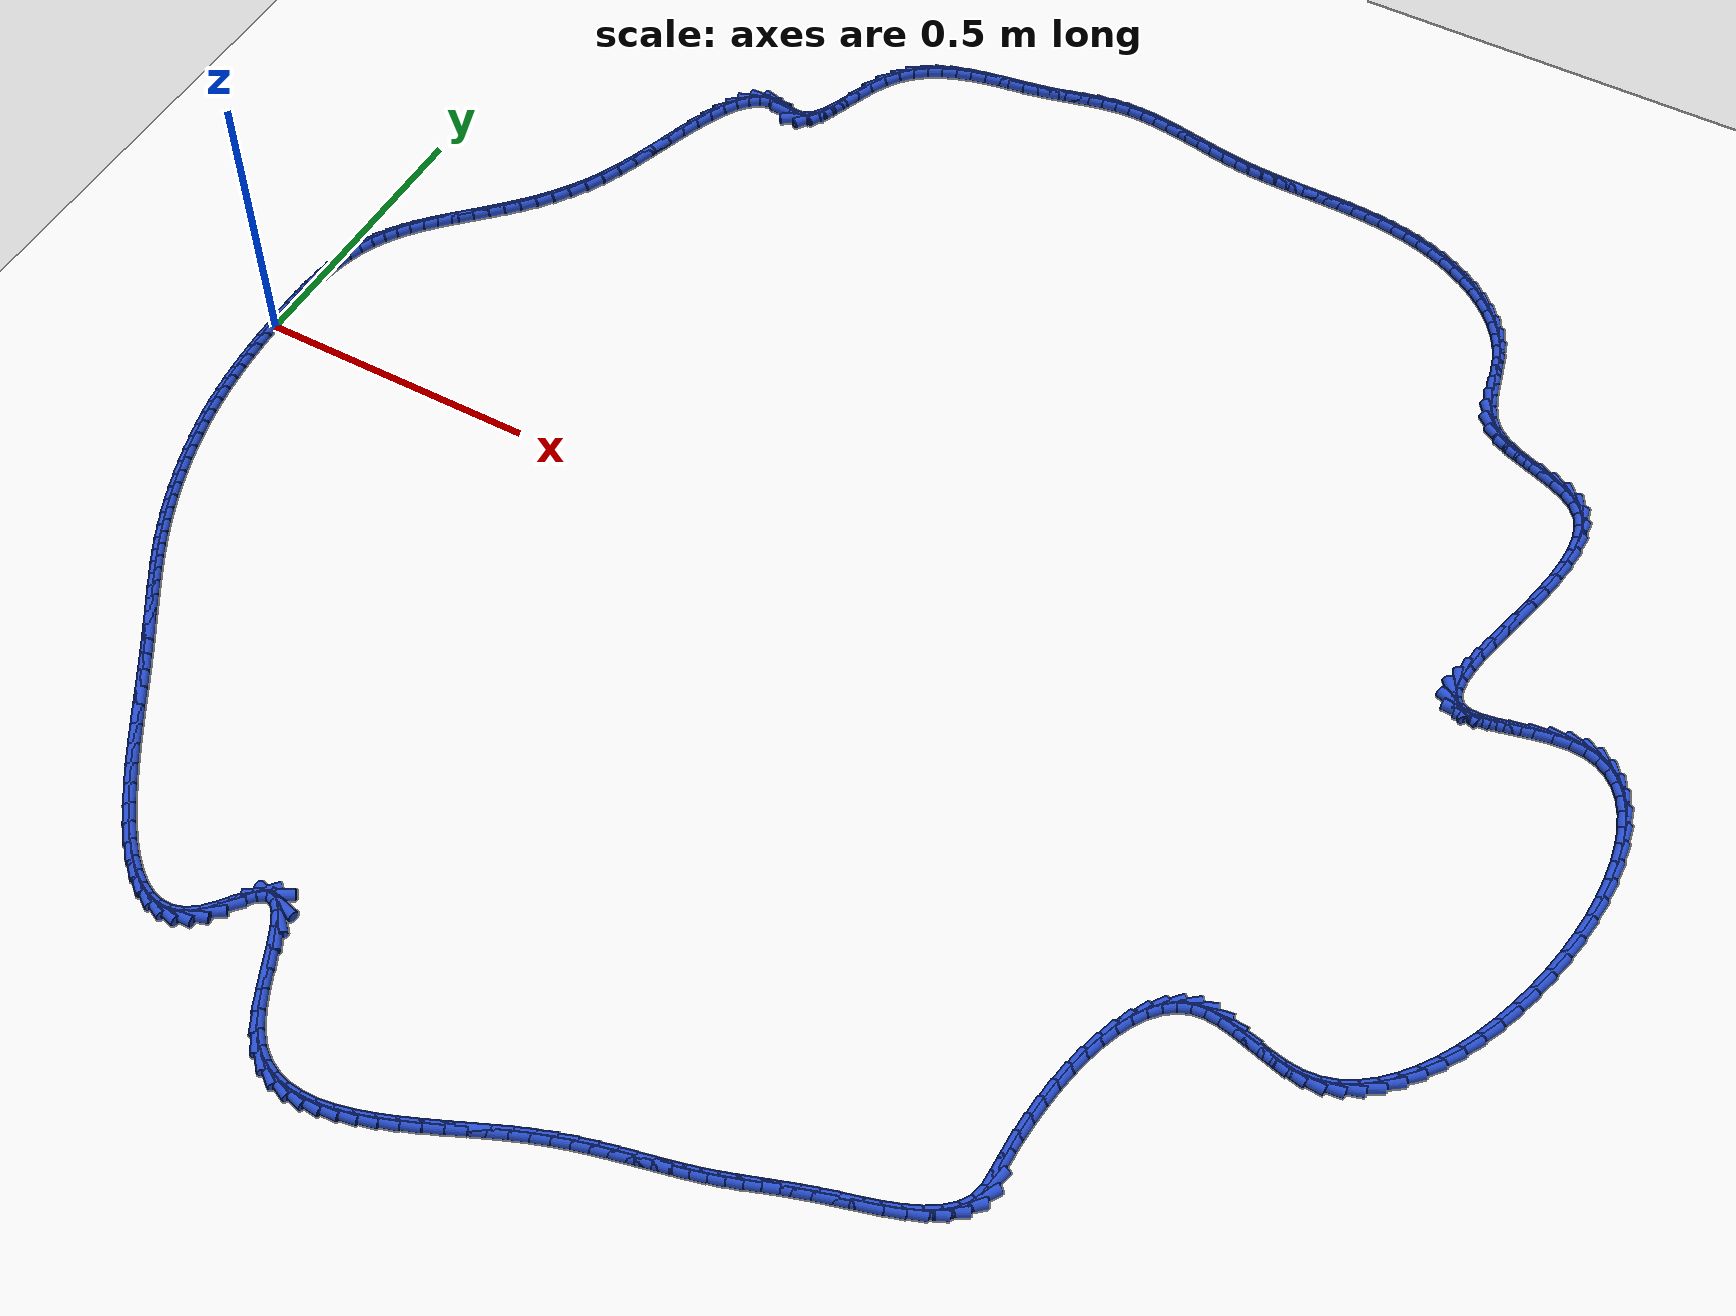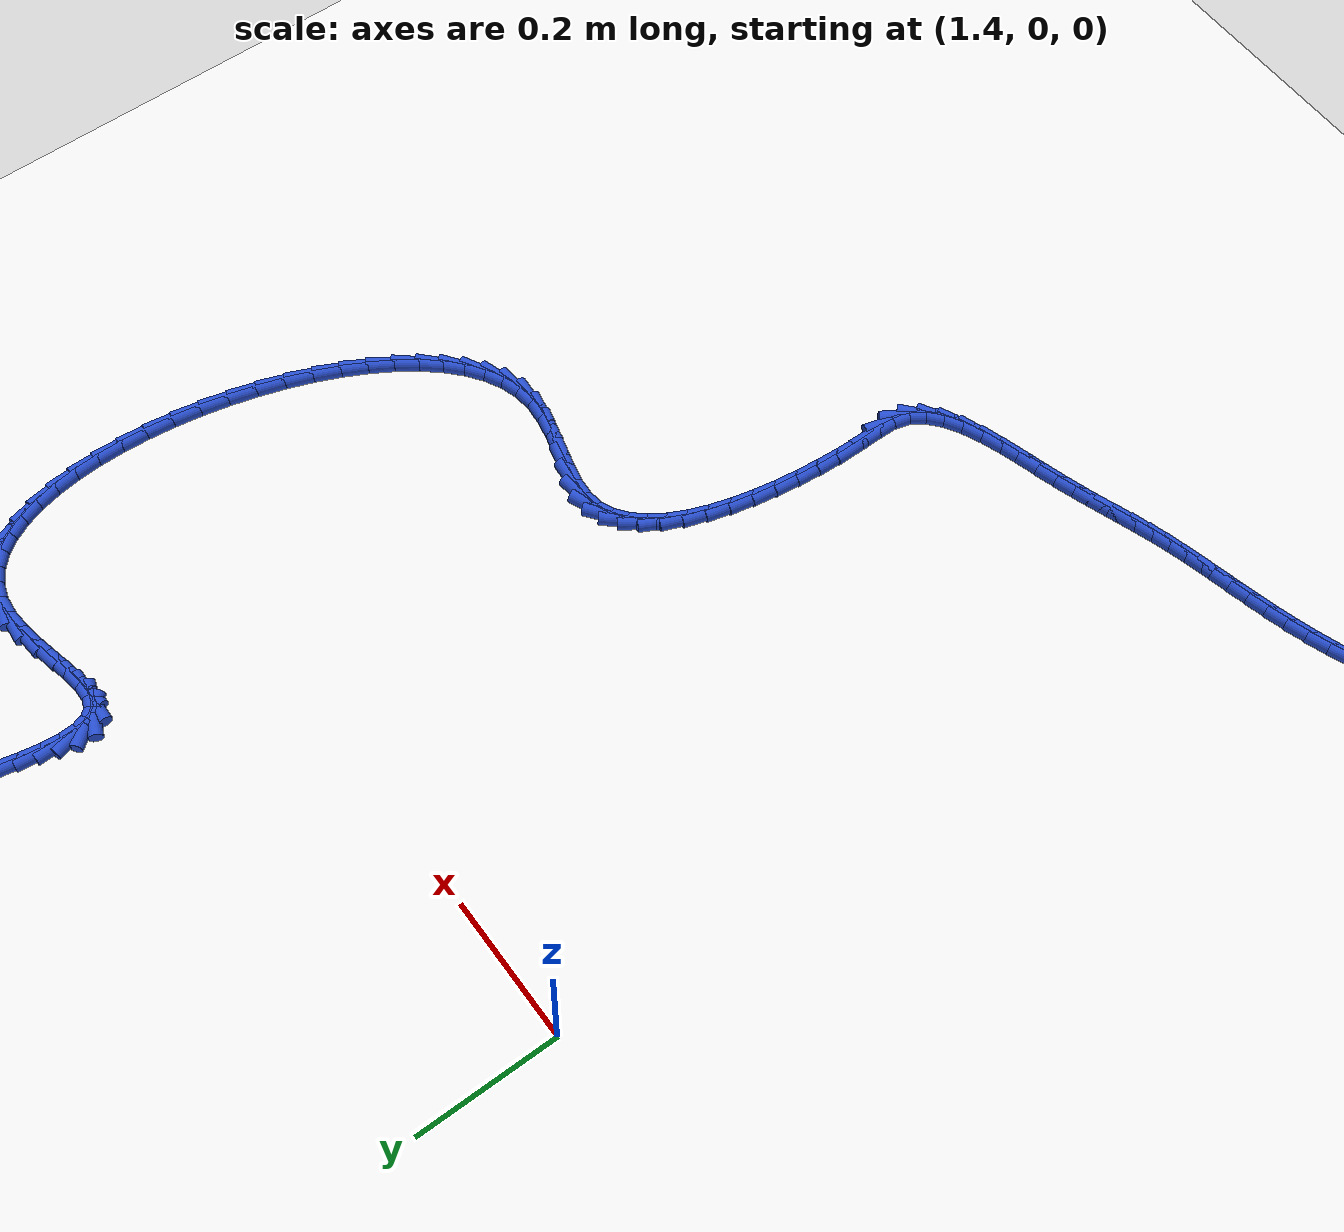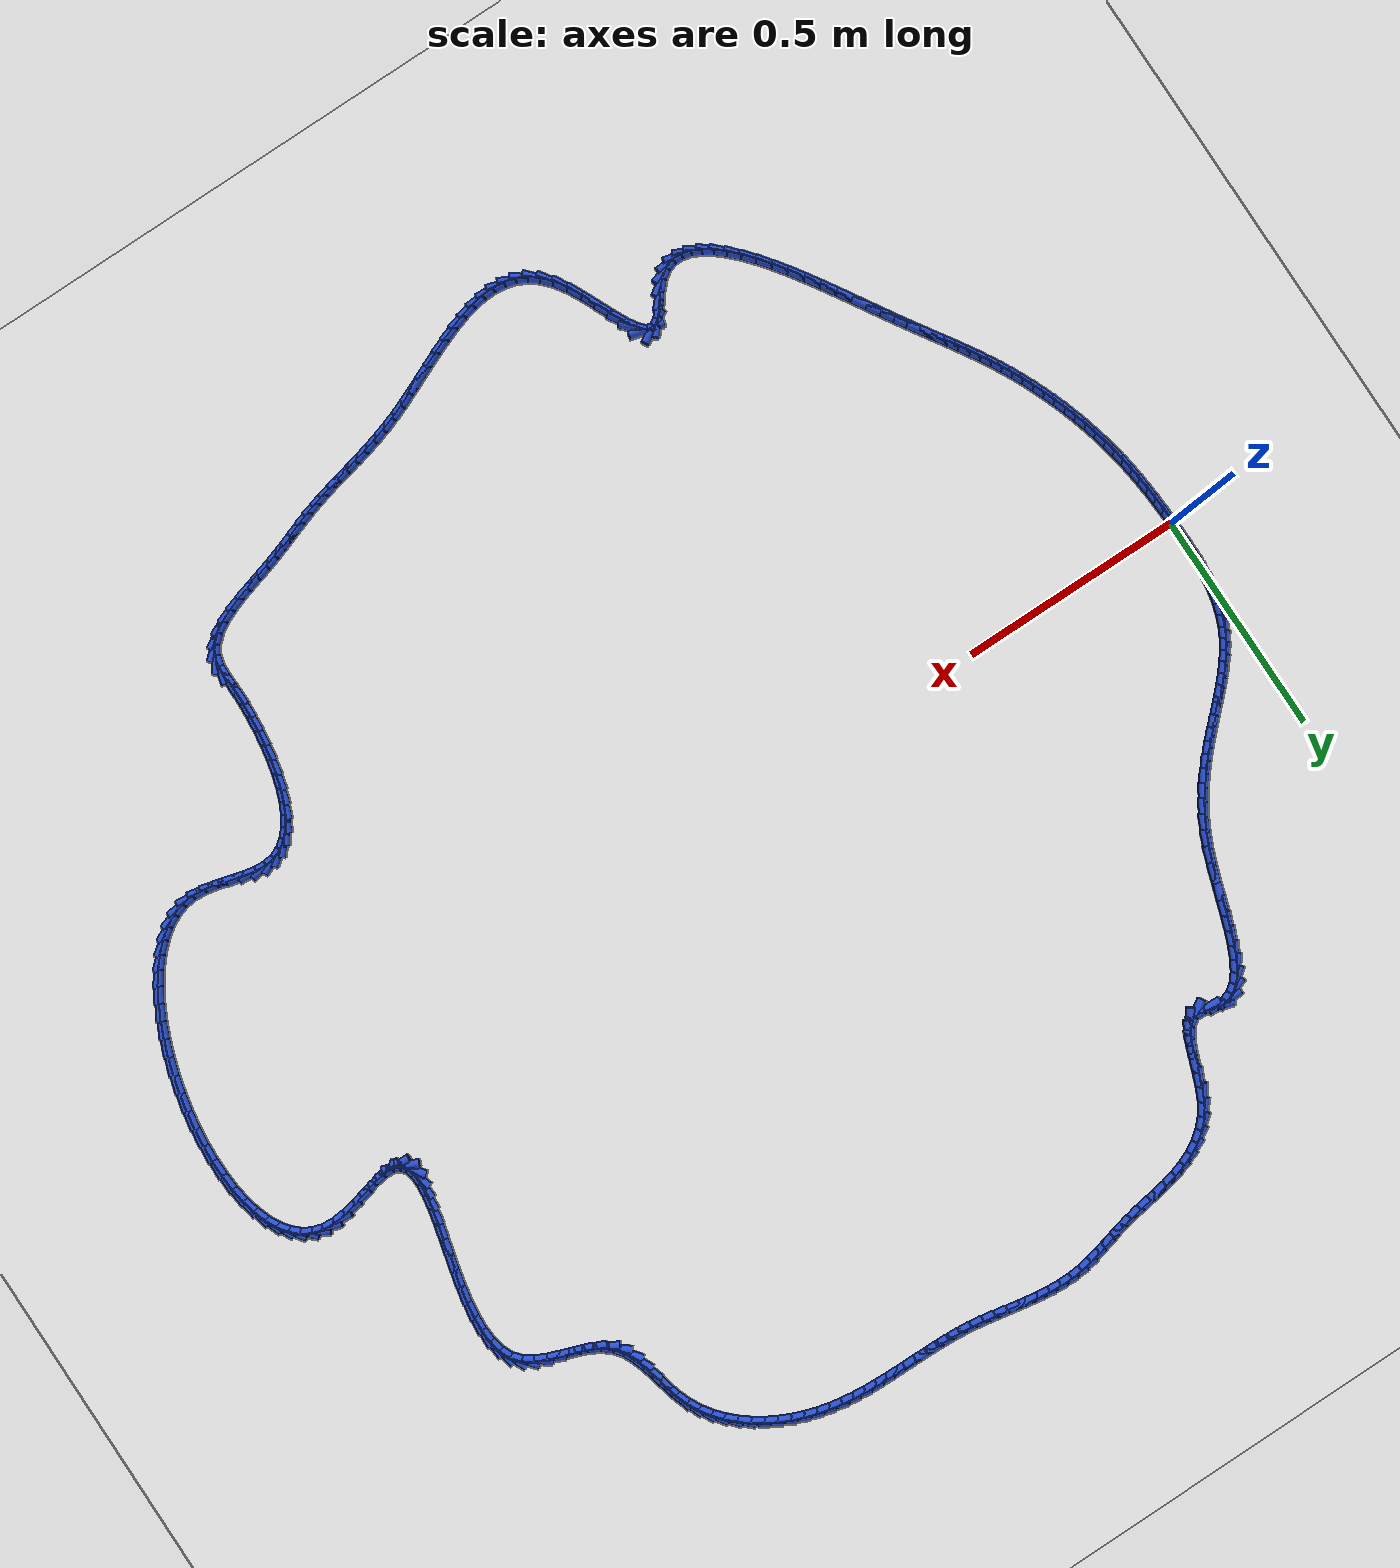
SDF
<sdf version="1.6">
 <world name="default">
  <light name="sun" type="directional">
   <pose>0 0 10 0 -0 0</pose>
   <diffuse>0.8 0.8 0.8 1</diffuse>
   <specular>0.2 0.2 0.2 1</specular>
   <attenuation>
    <range>1000</range>
    <constant>0.9</constant>
    <linear>0.01</linear>
    <quadratic>0.001</quadratic>
   </attenuation>
   <direction>-0.5 0.1 -0.9</direction>
  </light>
  <model name="ground_plane">
   <static>1</static>
   <link name="link">
    <collision name="collision">
     <geometry><plane><normal>0 0 1</normal><size>100 100</size></plane></geometry>
     <surface><friction><ode><mu>100</mu><mu2>50</mu2></ode></friction></surface>
    </collision>
    <visual name="visual">
     <cast_shadows>0</cast_shadows>
     <geometry><plane><normal>0 0 1</normal><size>100 100</size></plane></geometry>
     <material>
      <script><uri>file://media/materials/scripts/gazebo.material</uri><name>Gazebo/WhiteGlow</name></script>
     </material>
    </visual>
   </link>
  </model>
  <gravity>0 0 -9.8</gravity>
  <magnetic_field>6e-06 2.3e-05 -4.2e-05</magnetic_field>
  <atmosphere type="adiabatic"/>
  <physics name="default_physics" default="0" type="ode">
   <max_step_size>0.001</max_step_size>
   <real_time_factor>1</real_time_factor>
   <real_time_update_rate>1000</real_time_update_rate>
  </physics>
  <scene><ambient>0.4 0.4 0.4 1</ambient><background>0.7 0.7 0.7 1</background><shadows>1</shadows></scene>
  <spherical_coordinates>
   <surface_model>EARTH_WGS84</surface_model>
   <latitude_deg>0</latitude_deg>
   <longitude_deg>0</longitude_deg>
   <elevation>0</elevation>
   <heading_deg>0</heading_deg>
  </spherical_coordinates>
  <model name="line">
   <link name="link_0">
    <pose>-1.2685165418080402e-17 6.938893903907228e-18 0.01 0 1.57 -1.550461917488164</pose>
    <collision name="collision">
     <geometry><cylinder><radius>0.01</radius><length>0.08</length></cylinder></geometry>
    </collision>
    <visual name="visual">
     <material>
      <script><name>Gazebo/Blue</name><uri>file://media/materials/scripts/gazebo.material</uri></script>
     </material>
     <geometry><cylinder><radius>0.01</radius><length>0.08</length></cylinder></geometry>
    </visual>
   </link>
   <link name="link_1">
    <pose>-0.0005686694016888398 0.027962013136870672 0.01 0 1.57 -1.5706656132257417</pose>
    <collision name="collision">
     <geometry><cylinder><radius>0.01</radius><length>0.08</length></cylinder></geometry>
    </collision>
    <visual name="visual">
     <material>
      <script><name>Gazebo/Blue</name><uri>file://media/materials/scripts/gazebo.material</uri></script>
     </material>
     <geometry><cylinder><radius>0.01</radius><length>0.08</length></cylinder></geometry>
    </visual>
   </link>
   <link name="link_2">
    <pose>-0.0005723463543047523 0.05609185932457729 0.01 0 1.57 1.543689909033891</pose>
    <collision name="collision">
     <geometry><cylinder><radius>0.01</radius><length>0.08</length></cylinder></geometry>
    </collision>
    <visual name="visual">
     <material>
      <script><name>Gazebo/Blue</name><uri>file://media/materials/scripts/gazebo.material</uri></script>
     </material>
     <geometry><cylinder><radius>0.01</radius><length>0.08</length></cylinder></geometry>
    </visual>
   </link>
   <link name="link_3">
    <pose>0.00018867997017918132 0.084160486172686 0.01 0 1.57 1.5087614617827332</pose>
    <collision name="collision">
     <geometry><cylinder><radius>0.01</radius><length>0.08</length></cylinder></geometry>
    </collision>
    <visual name="visual">
     <material>
      <script><name>Gazebo/Blue</name><uri>file://media/materials/scripts/gazebo.material</uri></script>
     </material>
     <geometry><cylinder><radius>0.01</radius><length>0.08</length></cylinder></geometry>
    </visual>
   </link>
   <link name="link_4">
    <pose>0.001914120399789892 0.11193884129076302 0.01 0 1.57 1.4651867562117058</pose>
    <collision name="collision">
     <geometry><cylinder><radius>0.01</radius><length>0.08</length></cylinder></geometry>
    </collision>
    <visual name="visual">
     <material>
      <script><name>Gazebo/Blue</name><uri>file://media/materials/scripts/gazebo.material</uri></script>
     </material>
     <geometry><cylinder><radius>0.01</radius><length>0.08</length></cylinder></geometry>
    </visual>
   </link>
   <link name="link_5">
    <pose>0.00480368576255431 0.13919787228837457 0.01 0 1.57 1.4117109105173449</pose>
    <collision name="collision">
     <geometry><cylinder><radius>0.01</radius><length>0.08</length></cylinder></geometry>
    </collision>
    <visual name="visual">
     <material>
      <script><name>Gazebo/Blue</name><uri>file://media/materials/scripts/gazebo.material</uri></script>
     </material>
     <geometry><cylinder><radius>0.01</radius><length>0.08</length></cylinder></geometry>
    </visual>
   </link>
   <link name="link_6">
    <pose>0.009057086886499373 0.16570852677508685 0.01 0 1.57 1.3468005760545543</pose>
    <collision name="collision">
     <geometry><cylinder><radius>0.01</radius><length>0.08</length></cylinder></geometry>
    </collision>
    <visual name="visual">
     <material>
      <script><name>Gazebo/Blue</name><uri>file://media/materials/scripts/gazebo.material</uri></script>
     </material>
     <geometry><cylinder><radius>0.01</radius><length>0.08</length></cylinder></geometry>
    </visual>
   </link>
   <link name="link_7">
    <pose>0.014874034599652001 0.19124175236046598 0.01 0 1.57 1.2687319116251583</pose>
    <collision name="collision">
     <geometry><cylinder><radius>0.01</radius><length>0.08</length></cylinder></geometry>
    </collision>
    <visual name="visual">
     <material>
      <script><name>Gazebo/Blue</name><uri>file://media/materials/scripts/gazebo.material</uri></script>
     </material>
     <geometry><cylinder><radius>0.01</radius><length>0.08</length></cylinder></geometry>
    </visual>
   </link>
   <link name="link_8">
    <pose>0.02245423973003914 0.21556849665407823 0.01 0 1.57 1.1770892142023848</pose>
    <collision name="collision">
     <geometry><cylinder><radius>0.01</radius><length>0.08</length></cylinder></geometry>
    </collision>
    <visual name="visual">
     <material>
      <script><name>Gazebo/Blue</name><uri>file://media/materials/scripts/gazebo.material</uri></script>
     </material>
     <geometry><cylinder><radius>0.01</radius><length>0.08</length></cylinder></geometry>
    </visual>
   </link>
   <link name="link_9">
    <pose>0.031974073909105796 0.23848604095330644 0.01 0 1.57 1.0847701563713708</pose>
    <collision name="collision">
     <geometry><cylinder><radius>0.01</radius><length>0.08</length></cylinder></geometry>
    </collision>
    <visual name="visual">
     <material>
      <script><name>Gazebo/Blue</name><uri>file://media/materials/scripts/gazebo.material</uri></script>
     </material>
     <geometry><cylinder><radius>0.01</radius><length>0.08</length></cylinder></geometry>
    </visual>
   </link>
   <link name="link_10">
    <pose>0.04337170612993816 0.2600604313304327 0.01 0 1.57 1.0020567510092364</pose>
    <collision name="collision">
     <geometry><cylinder><radius>0.01</radius><length>0.08</length></cylinder></geometry>
    </collision>
    <visual name="visual">
     <material>
      <script><name>Gazebo/Blue</name><uri>file://media/materials/scripts/gazebo.material</uri></script>
     </material>
     <geometry><cylinder><radius>0.01</radius><length>0.08</length></cylinder></geometry>
    </visual>
   </link>
   <link name="link_11">
    <pose>0.05644601659074941 0.28051487383656154 0.01 0 1.57 0.9312873132012074</pose>
    <collision name="collision">
     <geometry><cylinder><radius>0.01</radius><length>0.08</length></cylinder></geometry>
    </collision>
    <visual name="visual">
     <material>
      <script><name>Gazebo/Blue</name><uri>file://media/materials/scripts/gazebo.material</uri></script>
     </material>
     <geometry><cylinder><radius>0.01</radius><length>0.08</length></cylinder></geometry>
    </visual>
   </link>
   <link name="link_12">
    <pose>0.07099413260315113 0.3000745523101815 0.01 0 1.57 0.873647891597159</pose>
    <collision name="collision">
     <geometry><cylinder><radius>0.01</radius><length>0.08</length></cylinder></geometry>
    </collision>
    <visual name="visual">
     <material>
      <script><name>Gazebo/Blue</name><uri>file://media/materials/scripts/gazebo.material</uri></script>
     </material>
     <geometry><cylinder><radius>0.01</radius><length>0.08</length></cylinder></geometry>
    </visual>
   </link>
   <link name="link_13">
    <pose>0.08681318147875483 0.31896465058978085 0.01 0 1.57 0.8294813563520967</pose>
    <collision name="collision">
     <geometry><cylinder><radius>0.01</radius><length>0.08</length></cylinder></geometry>
    </collision>
    <visual name="visual">
     <material>
      <script><name>Gazebo/Blue</name><uri>file://media/materials/scripts/gazebo.material</uri></script>
     </material>
     <geometry><cylinder><radius>0.01</radius><length>0.08</length></cylinder></geometry>
    </visual>
   </link>
   <link name="link_14">
    <pose>0.10370029052917212 0.337410352513848 0.01 0 1.57 0.7985771910868928</pose>
    <collision name="collision">
     <geometry><cylinder><radius>0.01</radius><length>0.08</length></cylinder></geometry>
    </collision>
    <visual name="visual">
     <material>
      <script><name>Gazebo/Blue</name><uri>file://media/materials/scripts/gazebo.material</uri></script>
     </material>
     <geometry><cylinder><radius>0.01</radius><length>0.08</length></cylinder></geometry>
    </visual>
   </link>
   <link name="link_15">
    <pose>0.12145258706601467 0.35563684192087136 0.01 0 1.57 0.7804278043434967</pose>
    <collision name="collision">
     <geometry><cylinder><radius>0.01</radius><length>0.08</length></cylinder></geometry>
    </collision>
    <visual name="visual">
     <material>
      <script><name>Gazebo/Blue</name><uri>file://media/materials/scripts/gazebo.material</uri></script>
     </material>
     <geometry><cylinder><radius>0.01</radius><length>0.08</length></cylinder></geometry>
    </visual>
   </link>
   <link name="link_16">
    <pose>0.13986719840089393 0.37386930264933926 0.01 0 1.57 0.774406019735312</pose>
    <collision name="collision">
     <geometry><cylinder><radius>0.01</radius><length>0.08</length></cylinder></geometry>
    </collision>
    <visual name="visual">
     <material>
      <script><name>Gazebo/Blue</name><uri>file://media/materials/scripts/gazebo.material</uri></script>
     </material>
     <geometry><cylinder><radius>0.01</radius><length>0.08</length></cylinder></geometry>
    </visual>
   </link>
   <link name="link_17">
    <pose>0.15874125184542148 0.39233291853774016 0.01 0 1.57 0.779861694862554</pose>
    <collision name="collision">
     <geometry><cylinder><radius>0.01</radius><length>0.08</length></cylinder></geometry>
    </collision>
    <visual name="visual">
     <material>
      <script><name>Gazebo/Blue</name><uri>file://media/materials/scripts/gazebo.material</uri></script>
     </material>
     <geometry><cylinder><radius>0.01</radius><length>0.08</length></cylinder></geometry>
    </visual>
   </link>
   <link name="link_18">
    <pose>0.177871874711209 0.41125287342456246 0.01 0 1.57 0.7961531837774716</pose>
    <collision name="collision">
     <geometry><cylinder><radius>0.01</radius><length>0.08</length></cylinder></geometry>
    </collision>
    <visual name="visual">
     <material>
      <script><name>Gazebo/Blue</name><uri>file://media/materials/scripts/gazebo.material</uri></script>
     </material>
     <geometry><cylinder><radius>0.01</radius><length>0.08</length></cylinder></geometry>
    </visual>
   </link>
   <link name="link_19">
    <pose>0.19705619430986798 0.43085435114829446 0.01 0 1.57 0.8226322566231087</pose>
    <collision name="collision">
     <geometry><cylinder><radius>0.01</radius><length>0.08</length></cylinder></geometry>
    </collision>
    <visual name="visual">
     <material>
      <script><name>Gazebo/Blue</name><uri>file://media/materials/scripts/gazebo.material</uri></script>
     </material>
     <geometry><cylinder><radius>0.01</radius><length>0.08</length></cylinder></geometry>
    </visual>
   </link>
   <link name="link_20">
    <pose>0.21609133795300994 0.45136253554742445 0.01 0 1.57 0.8585991663227327</pose>
    <collision name="collision">
     <geometry><cylinder><radius>0.01</radius><length>0.08</length></cylinder></geometry>
    </collision>
    <visual name="visual">
     <material>
      <script><name>Gazebo/Blue</name><uri>file://media/materials/scripts/gazebo.material</uri></script>
     </material>
     <geometry><cylinder><radius>0.01</radius><length>0.08</length></cylinder></geometry>
    </visual>
   </link>
   <link name="link_21">
    <pose>0.23477443295224665 0.4730026104604412 0.01 0 1.57 0.9032432070917864</pose>
    <collision name="collision">
     <geometry><cylinder><radius>0.01</radius><length>0.08</length></cylinder></geometry>
    </collision>
    <visual name="visual">
     <material>
      <script><name>Gazebo/Blue</name><uri>file://media/materials/scripts/gazebo.material</uri></script>
     </material>
     <geometry><cylinder><radius>0.01</radius><length>0.08</length></cylinder></geometry>
    </visual>
   </link>
   <link name="link_22">
    <pose>0.2529026066191895 0.4959997597258326 0.01 0 1.57 0.9555848078862658</pose>
    <collision name="collision">
     <geometry><cylinder><radius>0.01</radius><length>0.08</length></cylinder></geometry>
    </collision>
    <visual name="visual">
     <material>
      <script><name>Gazebo/Blue</name><uri>file://media/materials/scripts/gazebo.material</uri></script>
     </material>
     <geometry><cylinder><radius>0.01</radius><length>0.08</length></cylinder></geometry>
    </visual>
   </link>
   <link name="link_23">
    <pose>0.2702729862654501 0.5205791671820873 0.01 0 1.57 1.0144366761378216</pose>
    <collision name="collision">
     <geometry><cylinder><radius>0.01</radius><length>0.08</length></cylinder></geometry>
    </collision>
    <visual name="visual">
     <material>
      <script><name>Gazebo/Blue</name><uri>file://media/materials/scripts/gazebo.material</uri></script>
     </material>
     <geometry><cylinder><radius>0.01</radius><length>0.08</length></cylinder></geometry>
    </visual>
   </link>
   <link name="link_24">
    <pose>0.28668269920264006 0.5469660166676936 0.01 0 1.57 1.0784007524170993</pose>
    <collision name="collision">
     <geometry><cylinder><radius>0.01</radius><length>0.08</length></cylinder></geometry>
    </collision>
    <visual name="visual">
     <material>
      <script><name>Gazebo/Blue</name><uri>file://media/materials/scripts/gazebo.material</uri></script>
     </material>
     <geometry><cylinder><radius>0.01</radius><length>0.08</length></cylinder></geometry>
    </visual>
   </link>
   <link name="link_25">
    <pose>0.3019288727423709 0.5753854920211401 0.01 0 1.57 1.1450240405955046</pose>
    <collision name="collision">
     <geometry><cylinder><radius>0.01</radius><length>0.08</length></cylinder></geometry>
    </collision>
    <visual name="visual">
     <material>
      <script><name>Gazebo/Blue</name><uri>file://media/materials/scripts/gazebo.material</uri></script>
     </material>
     <geometry><cylinder><radius>0.01</radius><length>0.08</length></cylinder></geometry>
    </visual>
   </link>
   <link name="link_26">
    <pose>0.31582645677261895 0.6060297179542492 0.01 0 1.57 1.1996217235226938</pose>
    <collision name="collision">
     <geometry><cylinder><radius>0.01</radius><length>0.08</length></cylinder></geometry>
    </collision>
    <visual name="visual">
     <material>
      <script><name>Gazebo/Blue</name><uri>file://media/materials/scripts/gazebo.material</uri></script>
     </material>
     <geometry><cylinder><radius>0.01</radius><length>0.08</length></cylinder></geometry>
    </visual>
   </link>
   <link name="link_27">
    <pose>0.3284830538619791 0.6385479772327747 0.01 0 1.57 1.234031111099753</pose>
    <collision name="collision">
     <geometry><cylinder><radius>0.01</radius><length>0.08</length></cylinder></geometry>
    </collision>
    <visual name="visual">
     <material>
      <script><name>Gazebo/Blue</name><uri>file://media/materials/scripts/gazebo.material</uri></script>
     </material>
     <geometry><cylinder><radius>0.01</radius><length>0.08</length></cylinder></geometry>
    </visual>
   </link>
   <link name="link_28">
    <pose>0.34024562153304766 0.6721455727185245 0.01 0 1.57 1.2508327753435502</pose>
    <collision name="collision">
     <geometry><cylinder><radius>0.01</radius><length>0.08</length></cylinder></geometry>
    </collision>
    <visual name="visual">
     <material>
      <script><name>Gazebo/Blue</name><uri>file://media/materials/scripts/gazebo.material</uri></script>
     </material>
     <geometry><cylinder><radius>0.01</radius><length>0.08</length></cylinder></geometry>
    </visual>
   </link>
   <link name="link_29">
    <pose>0.3514681451042997 0.7060147714029928 0.01 0 1.57 1.2510602079354796</pose>
    <collision name="collision">
     <geometry><cylinder><radius>0.01</radius><length>0.08</length></cylinder></geometry>
    </collision>
    <visual name="visual">
     <material>
      <script><name>Gazebo/Blue</name><uri>file://media/materials/scripts/gazebo.material</uri></script>
     </material>
     <geometry><cylinder><radius>0.01</radius><length>0.08</length></cylinder></geometry>
    </visual>
   </link>
   <link name="link_30">
    <pose>0.36250460989421 0.7393478402776732 0.01 0 1.57 1.2338940209659408</pose>
    <collision name="collision">
     <geometry><cylinder><radius>0.01</radius><length>0.08</length></cylinder></geometry>
    </collision>
    <visual name="visual">
     <material>
      <script><name>Gazebo/Blue</name><uri>file://media/materials/scripts/gazebo.material</uri></script>
     </material>
     <geometry><cylinder><radius>0.01</radius><length>0.08</length></cylinder></geometry>
    </visual>
   </link>
   <link name="link_31">
    <pose>0.37370900122125383 0.7713370463340598 0.01 0 1.57 1.1963354076063053</pose>
    <collision name="collision">
     <geometry><cylinder><radius>0.01</radius><length>0.08</length></cylinder></geometry>
    </collision>
    <visual name="visual">
     <material>
      <script><name>Gazebo/Blue</name><uri>file://media/materials/scripts/gazebo.material</uri></script>
     </material>
     <geometry><cylinder><radius>0.01</radius><length>0.08</length></cylinder></geometry>
    </visual>
   </link>
   <link name="link_32">
    <pose>0.3854353044039061 0.8011746565636464 0.01 0 1.57 1.1323680816675554</pose>
    <collision name="collision">
     <geometry><cylinder><radius>0.01</radius><length>0.08</length></cylinder></geometry>
    </collision>
    <visual name="visual">
     <material>
      <script><name>Gazebo/Blue</name><uri>file://media/materials/scripts/gazebo.material</uri></script>
     </material>
     <geometry><cylinder><radius>0.01</radius><length>0.08</length></cylinder></geometry>
    </visual>
   </link>
   <link name="link_33">
    <pose>0.39803750476064204 0.8280529379579274 0.01 0 1.57 1.0314799258332108</pose>
    <collision name="collision">
     <geometry><cylinder><radius>0.01</radius><length>0.08</length></cylinder></geometry>
    </collision>
    <visual name="visual">
     <material>
      <script><name>Gazebo/Blue</name><uri>file://media/materials/scripts/gazebo.material</uri></script>
     </material>
     <geometry><cylinder><radius>0.01</radius><length>0.08</length></cylinder></geometry>
    </visual>
   </link>
   <link name="link_34">
    <pose>0.41186958760993647 0.8511641575083962 0.01 0 1.57 0.8770480726345231</pose>
    <collision name="collision">
     <geometry><cylinder><radius>0.01</radius><length>0.08</length></cylinder></geometry>
    </collision>
    <visual name="visual">
     <material>
      <script><name>Gazebo/Blue</name><uri>file://media/materials/scripts/gazebo.material</uri></script>
     </material>
     <geometry><cylinder><radius>0.01</radius><length>0.08</length></cylinder></geometry>
    </visual>
   </link>
   <link name="link_35">
    <pose>0.4272855382702645 0.8697005822065469 0.01 0 1.57 0.6485909962280908</pose>
    <collision name="collision">
     <geometry><cylinder><radius>0.01</radius><length>0.08</length></cylinder></geometry>
    </collision>
    <visual name="visual">
     <material>
      <script><name>Gazebo/Blue</name><uri>file://media/materials/scripts/gazebo.material</uri></script>
     </material>
     <geometry><cylinder><radius>0.01</radius><length>0.08</length></cylinder></geometry>
    </visual>
   </link>
   <link name="link_36">
    <pose>0.44463934206010103 0.8828544790438733 0.01 0 1.57 0.34064443684874574</pose>
    <collision name="collision">
     <geometry><cylinder><radius>0.01</radius><length>0.08</length></cylinder></geometry>
    </collision>
    <visual name="visual">
     <material>
      <script><name>Gazebo/Blue</name><uri>file://media/materials/scripts/gazebo.material</uri></script>
     </material>
     <geometry><cylinder><radius>0.01</radius><length>0.08</length></cylinder></geometry>
    </visual>
   </link>
   <link name="link_37">
    <pose>0.46428498429792153 0.8898181150118699 0.01 0 1.57 -0.0015413020671682885</pose>
    <collision name="collision">
     <geometry><cylinder><radius>0.01</radius><length>0.08</length></cylinder></geometry>
    </collision>
    <visual name="visual">
     <material>
      <script><name>Gazebo/Blue</name><uri>file://media/materials/scripts/gazebo.material</uri></script>
     </material>
     <geometry><cylinder><radius>0.01</radius><length>0.08</length></cylinder></geometry>
    </visual>
   </link>
   <link name="link_38">
    <pose>0.4865764503022006 0.8897837571020303 0.01 0 1.57 -0.2820985060791833</pose>
    <collision name="collision">
     <geometry><cylinder><radius>0.01</radius><length>0.08</length></cylinder></geometry>
    </collision>
    <visual name="visual">
     <material>
      <script><name>Gazebo/Blue</name><uri>file://media/materials/scripts/gazebo.material</uri></script>
     </material>
     <geometry><cylinder><radius>0.01</radius><length>0.08</length></cylinder></geometry>
    </visual>
   </link>
   <link name="link_39">
    <pose>0.5116502056068317 0.8825166875895156 0.01 0 1.57 -0.03689186048376572</pose>
    <collision name="collision">
     <geometry><cylinder><radius>0.01</radius><length>0.08</length></cylinder></geometry>
    </collision>
    <visual name="visual">
     <material>
      <script><name>Gazebo/Blue</name><uri>file://media/materials/scripts/gazebo.material</uri></script>
     </material>
     <geometry><cylinder><radius>0.01</radius><length>0.08</length></cylinder></geometry>
    </visual>
   </link>
   <link name="link_40">
    <pose>0.5343771367277692 0.8816778682358448 0.01 0 1.57 0.5748294485380433</pose>
    <collision name="collision">
     <geometry><cylinder><radius>0.01</radius><length>0.08</length></cylinder></geometry>
    </collision>
    <visual name="visual">
     <material>
      <script><name>Gazebo/Blue</name><uri>file://media/materials/scripts/gazebo.material</uri></script>
     </material>
     <geometry><cylinder><radius>0.01</radius><length>0.08</length></cylinder></geometry>
    </visual>
   </link>
   <link name="link_41">
    <pose>0.5525231641808566 0.8934329255111289 0.01 0 1.57 0.9642928579131175</pose>
    <collision name="collision">
     <geometry><cylinder><radius>0.01</radius><length>0.08</length></cylinder></geometry>
    </collision>
    <visual name="visual">
     <material>
      <script><name>Gazebo/Blue</name><uri>file://media/materials/scripts/gazebo.material</uri></script>
     </material>
     <geometry><cylinder><radius>0.01</radius><length>0.08</length></cylinder></geometry>
    </visual>
   </link>
   <link name="link_42">
    <pose>0.5673442339117954 0.9147973383610759 0.01 0 1.57 1.1431099076795346</pose>
    <collision name="collision">
     <geometry><cylinder><radius>0.01</radius><length>0.08</length></cylinder></geometry>
    </collision>
    <visual name="visual">
     <material>
      <script><name>Gazebo/Blue</name><uri>file://media/materials/scripts/gazebo.material</uri></script>
     </material>
     <geometry><cylinder><radius>0.01</radius><length>0.08</length></cylinder></geometry>
    </visual>
   </link>
   <link name="link_43">
    <pose>0.5800990728211286 0.942779289707718 0.01 0 1.57 1.2094082300645235</pose>
    <collision name="collision">
     <geometry><cylinder><radius>0.01</radius><length>0.08</length></cylinder></geometry>
    </collision>
    <visual name="visual">
     <material>
      <script><name>Gazebo/Blue</name><uri>file://media/materials/scripts/gazebo.material</uri></script>
     </material>
     <geometry><cylinder><radius>0.01</radius><length>0.08</length></cylinder></geometry>
    </visual>
   </link>
   <link name="link_44">
    <pose>0.5920464078093989 0.9743869624730861 0.01 0 1.57 1.2036778455167993</pose>
    <collision name="collision">
     <geometry><cylinder><radius>0.01</radius><length>0.08</length></cylinder></geometry>
    </collision>
    <visual name="visual">
     <material>
      <script><name>Gazebo/Blue</name><uri>file://media/materials/scripts/gazebo.material</uri></script>
     </material>
     <geometry><cylinder><radius>0.01</radius><length>0.08</length></cylinder></geometry>
    </visual>
   </link>
   <link name="link_45">
    <pose>0.6044449657771477 1.0066285395792107 0.01 0 1.57 1.1297113282340545</pose>
    <collision name="collision">
     <geometry><cylinder><radius>0.01</radius><length>0.08</length></cylinder></geometry>
    </collision>
    <visual name="visual">
     <material>
      <script><name>Gazebo/Blue</name><uri>file://media/materials/scripts/gazebo.material</uri></script>
     </material>
     <geometry><cylinder><radius>0.01</radius><length>0.08</length></cylinder></geometry>
    </visual>
   </link>
   <link name="link_46">
    <pose>0.6185533619596426 1.0365124553978236 0.01 0 1.57 0.9854082206253628</pose>
    <collision name="collision">
     <geometry><cylinder><radius>0.01</radius><length>0.08</length></cylinder></geometry>
    </collision>
    <visual name="visual">
     <material>
      <script><name>Gazebo/Blue</name><uri>file://media/materials/scripts/gazebo.material</uri></script>
     </material>
     <geometry><cylinder><radius>0.01</radius><length>0.08</length></cylinder></geometry>
    </visual>
   </link>
   <link name="link_47">
    <pose>0.6353041083996139 1.0617814688200229 0.01 0 1.57 0.8218741246418009</pose>
    <collision name="collision">
     <geometry><cylinder><radius>0.01</radius><length>0.08</length></cylinder></geometry>
    </collision>
    <visual name="visual">
     <material>
      <script><name>Gazebo/Blue</name><uri>file://media/materials/scripts/gazebo.material</uri></script>
     </material>
     <geometry><cylinder><radius>0.01</radius><length>0.08</length></cylinder></geometry>
    </visual>
   </link>
   <link name="link_48">
    <pose>0.6545874013089606 1.0825254426261772 0.01 0 1.57 0.6626611517887325</pose>
    <collision name="collision">
     <geometry><cylinder><radius>0.01</radius><length>0.08</length></cylinder></geometry>
    </collision>
    <visual name="visual">
     <material>
      <script><name>Gazebo/Blue</name><uri>file://media/materials/scripts/gazebo.material</uri></script>
     </material>
     <geometry><cylinder><radius>0.01</radius><length>0.08</length></cylinder></geometry>
    </visual>
   </link>
   <link name="link_49">
    <pose>0.6760856297458828 1.099302183154871 0.01 0 1.57 0.5190954004869909</pose>
    <collision name="collision">
     <geometry><cylinder><radius>0.01</radius><length>0.08</length></cylinder></geometry>
    </collision>
    <visual name="visual">
     <material>
      <script><name>Gazebo/Blue</name><uri>file://media/materials/scripts/gazebo.material</uri></script>
     </material>
     <geometry><cylinder><radius>0.01</radius><length>0.08</length></cylinder></geometry>
    </visual>
   </link>
   <link name="link_50">
    <pose>0.6994811827685814 1.112669496744689 0.01 0 1.57 0.3985153455276044</pose>
    <collision name="collision">
     <geometry><cylinder><radius>0.01</radius><length>0.08</length></cylinder></geometry>
    </collision>
    <visual name="visual">
     <material>
      <script><name>Gazebo/Blue</name><uri>file://media/materials/scripts/gazebo.material</uri></script>
     </material>
     <geometry><cylinder><radius>0.01</radius><length>0.08</length></cylinder></geometry>
    </visual>
   </link>
   <link name="link_51">
    <pose>0.7244564494352566 1.1231851897342162 0.01 0 1.57 0.30367290693040244</pose>
    <collision name="collision">
     <geometry><cylinder><radius>0.01</radius><length>0.08</length></cylinder></geometry>
    </collision>
    <visual name="visual">
     <material>
      <script><name>Gazebo/Blue</name><uri>file://media/materials/scripts/gazebo.material</uri></script>
     </material>
     <geometry><cylinder><radius>0.01</radius><length>0.08</length></cylinder></geometry>
    </visual>
   </link>
   <link name="link_52">
    <pose>0.7506938188041083 1.1314070684620359 0.01 0 1.57 0.23423051114752255</pose>
    <collision name="collision">
     <geometry><cylinder><radius>0.01</radius><length>0.08</length></cylinder></geometry>
    </collision>
    <visual name="visual">
     <material>
      <script><name>Gazebo/Blue</name><uri>file://media/materials/scripts/gazebo.material</uri></script>
     </material>
     <geometry><cylinder><radius>0.01</radius><length>0.08</length></cylinder></geometry>
    </visual>
   </link>
   <link name="link_53">
    <pose>0.7778756799333373 1.1378929392667338 0.01 0 1.57 0.18859506858207967</pose>
    <collision name="collision">
     <geometry><cylinder><radius>0.01</radius><length>0.08</length></cylinder></geometry>
    </collision>
    <visual name="visual">
     <material>
      <script><name>Gazebo/Blue</name><uri>file://media/materials/scripts/gazebo.material</uri></script>
     </material>
     <geometry><cylinder><radius>0.01</radius><length>0.08</length></cylinder></geometry>
    </visual>
   </link>
   <link name="link_54">
    <pose>0.8056844218811434 1.1432006084868935 0.01 0 1.57 0.1651811582211865</pose>
    <collision name="collision">
     <geometry><cylinder><radius>0.01</radius><length>0.08</length></cylinder></geometry>
    </collision>
    <visual name="visual">
     <material>
      <script><name>Gazebo/Blue</name><uri>file://media/materials/scripts/gazebo.material</uri></script>
     </material>
     <geometry><cylinder><radius>0.01</radius><length>0.08</length></cylinder></geometry>
    </visual>
   </link>
   <link name="link_55">
    <pose>0.8338024337057279 1.1478878824611007 0.01 0 1.57 0.16306214590424406</pose>
    <collision name="collision">
     <geometry><cylinder><radius>0.01</radius><length>0.08</length></cylinder></geometry>
    </collision>
    <visual name="visual">
     <material>
      <script><name>Gazebo/Blue</name><uri>file://media/materials/scripts/gazebo.material</uri></script>
     </material>
     <geometry><cylinder><radius>0.01</radius><length>0.08</length></cylinder></geometry>
    </visual>
   </link>
   <link name="link_56">
    <pose>0.8619121044652902 1.1525125675279388 0.01 0 1.57 0.18223267684221986</pose>
    <collision name="collision">
     <geometry><cylinder><radius>0.01</radius><length>0.08</length></cylinder></geometry>
    </collision>
    <visual name="visual">
     <material>
      <script><name>Gazebo/Blue</name><uri>file://media/materials/scripts/gazebo.material</uri></script>
     </material>
     <geometry><cylinder><radius>0.01</radius><length>0.08</length></cylinder></geometry>
    </visual>
   </link>
   <link name="link_57">
    <pose>0.8896958232180312 1.1576324700259932 0.01 0 1.57 0.21848729477399853</pose>
    <collision name="collision">
     <geometry><cylinder><radius>0.01</radius><length>0.08</length></cylinder></geometry>
    </collision>
    <visual name="visual">
     <material>
      <script><name>Gazebo/Blue</name><uri>file://media/materials/scripts/gazebo.material</uri></script>
     </material>
     <geometry><cylinder><radius>0.01</radius><length>0.08</length></cylinder></geometry>
    </visual>
   </link>
   <link name="link_58">
    <pose>0.9168896363579215 1.1636703560956998 0.01 0 1.57 0.2420399223462987</pose>
    <collision name="collision">
     <geometry><cylinder><radius>0.01</radius><length>0.08</length></cylinder></geometry>
    </collision>
    <visual name="visual">
     <material>
      <script><name>Gazebo/Blue</name><uri>file://media/materials/scripts/gazebo.material</uri></script>
     </material>
     <geometry><cylinder><radius>0.01</radius><length>0.08</length></cylinder></geometry>
    </visual>
   </link>
   <link name="link_59">
    <pose>0.9435465077467529 1.1702514010721297 0.01 0 1.57 0.24087109244552238</pose>
    <collision name="collision">
     <geometry><cylinder><radius>0.01</radius><length>0.08</length></cylinder></geometry>
    </collision>
    <visual name="visual">
     <material>
      <script><name>Gazebo/Blue</name><uri>file://media/materials/scripts/gazebo.material</uri></script>
     </material>
     <geometry><cylinder><radius>0.01</radius><length>0.08</length></cylinder></geometry>
    </visual>
   </link>
   <link name="link_60">
    <pose>0.9698353405580692 1.176708994136469 0.01 0 1.57 0.21389174979281778</pose>
    <collision name="collision">
     <geometry><cylinder><radius>0.01</radius><length>0.08</length></cylinder></geometry>
    </collision>
    <visual name="visual">
     <material>
      <script><name>Gazebo/Blue</name><uri>file://media/materials/scripts/gazebo.material</uri></script>
     </material>
     <geometry><cylinder><radius>0.01</radius><length>0.08</length></cylinder></geometry>
    </visual>
   </link>
   <link name="link_61">
    <pose>0.9959252108068503 1.1823760894773447 0.01 0 1.57 0.16014980521952538</pose>
    <collision name="collision">
     <geometry><cylinder><radius>0.01</radius><length>0.08</length></cylinder></geometry>
    </collision>
    <visual name="visual">
     <material>
      <script><name>Gazebo/Blue</name><uri>file://media/materials/scripts/gazebo.material</uri></script>
     </material>
     <geometry><cylinder><radius>0.01</radius><length>0.08</length></cylinder></geometry>
    </visual>
   </link>
   <link name="link_62">
    <pose>1.021985194508077 1.186585641283385 0.01 0 1.57 0.08090081180231525</pose>
    <collision name="collision">
     <geometry><cylinder><radius>0.01</radius><length>0.08</length></cylinder></geometry>
    </collision>
    <visual name="visual">
     <material>
      <script><name>Gazebo/Blue</name><uri>file://media/materials/scripts/gazebo.material</uri></script>
     </material>
     <geometry><cylinder><radius>0.01</radius><length>0.08</length></cylinder></geometry>
    </visual>
   </link>
   <link name="link_63">
    <pose>1.0481773050919463 1.188709239256581 0.01 0 1.57 -0.0008533584031455434</pose>
    <collision name="collision">
     <geometry><cylinder><radius>0.01</radius><length>0.08</length></cylinder></geometry>
    </collision>
    <visual name="visual">
     <material>
      <script><name>Gazebo/Blue</name><uri>file://media/materials/scripts/gazebo.material</uri></script>
     </material>
     <geometry><cylinder><radius>0.01</radius><length>0.08</length></cylinder></geometry>
    </visual>
   </link>
   <link name="link_64">
    <pose>1.074559679235587 1.1886867256304456 0.01 0 1.57 -0.06755084695265966</pose>
    <collision name="collision">
     <geometry><cylinder><radius>0.01</radius><length>0.08</length></cylinder></geometry>
    </collision>
    <visual name="visual">
     <material>
      <script><name>Gazebo/Blue</name><uri>file://media/materials/scripts/gazebo.material</uri></script>
     </material>
     <geometry><cylinder><radius>0.01</radius><length>0.08</length></cylinder></geometry>
    </visual>
   </link>
   <link name="link_65">
    <pose>1.1011114000294535 1.1868904012918973 0.01 0 1.57 -0.1188090589931766</pose>
    <collision name="collision">
     <geometry><cylinder><radius>0.01</radius><length>0.08</length></cylinder></geometry>
    </collision>
    <visual name="visual">
     <material>
      <script><name>Gazebo/Blue</name><uri>file://media/materials/scripts/gazebo.material</uri></script>
     </material>
     <geometry><cylinder><radius>0.01</radius><length>0.08</length></cylinder></geometry>
    </visual>
   </link>
   <link name="link_66">
    <pose>1.1278095689588863 1.1837034073985577 0.01 0 1.57 -0.15512880700084983</pose>
    <collision name="collision">
     <geometry><cylinder><radius>0.01</radius><length>0.08</length></cylinder></geometry>
    </collision>
    <visual name="visual">
     <material>
      <script><name>Gazebo/Blue</name><uri>file://media/materials/scripts/gazebo.material</uri></script>
     </material>
     <geometry><cylinder><radius>0.01</radius><length>0.08</length></cylinder></geometry>
    </visual>
   </link>
   <link name="link_67">
    <pose>1.1546312875092237 1.17950888510805 0.01 0 1.57 -0.17711714763510525</pose>
    <collision name="collision">
     <geometry><cylinder><radius>0.01</radius><length>0.08</length></cylinder></geometry>
    </collision>
    <visual name="visual">
     <material>
      <script><name>Gazebo/Blue</name><uri>file://media/materials/scripts/gazebo.material</uri></script>
     </material>
     <geometry><cylinder><radius>0.01</radius><length>0.08</length></cylinder></geometry>
    </visual>
   </link>
   <link name="link_68">
    <pose>1.1815536571658067 1.1746899755779956 0.01 0 1.57 -0.18526324865048763</pose>
    <collision name="collision">
     <geometry><cylinder><radius>0.01</radius><length>0.08</length></cylinder></geometry>
    </collision>
    <visual name="visual">
     <material>
      <script><name>Gazebo/Blue</name><uri>file://media/materials/scripts/gazebo.material</uri></script>
     </material>
     <geometry><cylinder><radius>0.01</radius><length>0.08</length></cylinder></geometry>
    </visual>
   </link>
   <link name="link_69">
    <pose>1.2085537794139747 1.1696298199660176 0.01 0 1.57 -0.17982394373652733</pose>
    <collision name="collision">
     <geometry><cylinder><radius>0.01</radius><length>0.08</length></cylinder></geometry>
    </collision>
    <visual name="visual">
     <material>
      <script><name>Gazebo/Blue</name><uri>file://media/materials/scripts/gazebo.material</uri></script>
     </material>
     <geometry><cylinder><radius>0.01</radius><length>0.08</length></cylinder></geometry>
    </visual>
   </link>
   <link name="link_70">
    <pose>1.2356087557390671 1.1647115594297375 0.01 0 1.57 -0.16078967873257932</pose>
    <collision name="collision">
     <geometry><cylinder><radius>0.01</radius><length>0.08</length></cylinder></geometry>
    </collision>
    <visual name="visual">
     <material>
      <script><name>Gazebo/Blue</name><uri>file://media/materials/scripts/gazebo.material</uri></script>
     </material>
     <geometry><cylinder><radius>0.01</radius><length>0.08</length></cylinder></geometry>
    </visual>
   </link>
   <link name="link_71">
    <pose>1.2626956876264235 1.1603183351267772 0.01 0 1.57 -0.12803148840598597</pose>
    <collision name="collision">
     <geometry><cylinder><radius>0.01</radius><length>0.08</length></cylinder></geometry>
    </collision>
    <visual name="visual">
     <material>
      <script><name>Gazebo/Blue</name><uri>file://media/materials/scripts/gazebo.material</uri></script>
     </material>
     <geometry><cylinder><radius>0.01</radius><length>0.08</length></cylinder></geometry>
    </visual>
   </link>
   <link name="link_72">
    <pose>1.2897917710052533 1.1568301026060317 0.01 0 1.57 -0.08913488115919549</pose>
    <collision name="collision">
     <geometry><cylinder><radius>0.01</radius><length>0.08</length></cylinder></geometry>
    </collision>
    <visual name="visual">
     <material>
      <script><name>Gazebo/Blue</name><uri>file://media/materials/scripts/gazebo.material</uri></script>
     </material>
     <geometry><cylinder><radius>0.01</radius><length>0.08</length></cylinder></geometry>
    </visual>
   </link>
   <link name="link_73">
    <pose>1.3168806557968902 1.154409123098259 0.01 0 1.57 -0.057004540363658304</pose>
    <collision name="collision">
     <geometry><cylinder><radius>0.01</radius><length>0.08</length></cylinder></geometry>
    </collision>
    <visual name="visual">
     <material>
      <script><name>Gazebo/Blue</name><uri>file://media/materials/scripts/gazebo.material</uri></script>
     </material>
     <geometry><cylinder><radius>0.01</radius><length>0.08</length></cylinder></geometry>
    </visual>
   </link>
   <link name="link_74">
    <pose>1.343956476700726 1.1528640043798208 0.01 0 1.57 -0.03299326368305219</pose>
    <collision name="collision">
     <geometry><cylinder><radius>0.01</radius><length>0.08</length></cylinder></geometry>
    </collision>
    <visual name="visual">
     <material>
      <script><name>Gazebo/Blue</name><uri>file://media/materials/scripts/gazebo.material</uri></script>
     </material>
     <geometry><cylinder><radius>0.01</radius><length>0.08</length></cylinder></geometry>
    </visual>
   </link>
   <link name="link_75">
    <pose>1.3710143290031198 1.1519709534554425 0.01 0 1.57 -0.017189965091219093</pose>
    <collision name="collision">
     <geometry><cylinder><radius>0.01</radius><length>0.08</length></cylinder></geometry>
    </collision>
    <visual name="visual">
     <material>
      <script><name>Gazebo/Blue</name><uri>file://media/materials/scripts/gazebo.material</uri></script>
     </material>
     <geometry><cylinder><radius>0.01</radius><length>0.08</length></cylinder></geometry>
    </visual>
   </link>
   <link name="link_76">
    <pose>1.3980493079904308 1.1515061773298487 0.01 0 1.57 -0.009637661575018781</pose>
    <collision name="collision">
     <geometry><cylinder><radius>0.01</radius><length>0.08</length></cylinder></geometry>
    </collision>
    <visual name="visual">
     <material>
      <script><name>Gazebo/Blue</name><uri>file://media/materials/scripts/gazebo.material</uri></script>
     </material>
     <geometry><cylinder><radius>0.01</radius><length>0.08</length></cylinder></geometry>
    </visual>
   </link>
   <link name="link_77">
    <pose>1.425056508949019 1.151245883007767 0.01 0 1.57 -0.01036517124153411</pose>
    <collision name="collision">
     <geometry><cylinder><radius>0.01</radius><length>0.08</length></cylinder></geometry>
    </collision>
    <visual name="visual">
     <material>
      <script><name>Gazebo/Blue</name><uri>file://media/materials/scripts/gazebo.material</uri></script>
     </material>
     <geometry><cylinder><radius>0.01</radius><length>0.08</length></cylinder></geometry>
    </visual>
   </link>
   <link name="link_78">
    <pose>1.4520310271652435 1.1509662774939213 0.01 0 1.57 -0.019402511415847007</pose>
    <collision name="collision">
     <geometry><cylinder><radius>0.01</radius><length>0.08</length></cylinder></geometry>
    </collision>
    <visual name="visual">
     <material>
      <script><name>Gazebo/Blue</name><uri>file://media/materials/scripts/gazebo.material</uri></script>
     </material>
     <geometry><cylinder><radius>0.01</radius><length>0.08</length></cylinder></geometry>
    </visual>
   </link>
   <link name="link_79">
    <pose>1.4789679579254635 1.1504435677930385 0.01 0 1.57 -0.03677937423734696</pose>
    <collision name="collision">
     <geometry><cylinder><radius>0.01</radius><length>0.08</length></cylinder></geometry>
    </collision>
    <visual name="visual">
     <material>
      <script><name>Gazebo/Blue</name><uri>file://media/materials/scripts/gazebo.material</uri></script>
     </material>
     <geometry><cylinder><radius>0.01</radius><length>0.08</length></cylinder></geometry>
    </visual>
   </link>
   <link name="link_80">
    <pose>1.5058623965160378 1.1494539609098438 0.01 0 1.57 -0.06250625986233037</pose>
    <collision name="collision">
     <geometry><cylinder><radius>0.01</radius><length>0.08</length></cylinder></geometry>
    </collision>
    <visual name="visual">
     <material>
      <script><name>Gazebo/Blue</name><uri>file://media/materials/scripts/gazebo.material</uri></script>
     </material>
     <geometry><cylinder><radius>0.01</radius><length>0.08</length></cylinder></geometry>
    </visual>
   </link>
   <link name="link_81">
    <pose>1.532709438223327 1.1477736638490628 0.01 0 1.57 -0.09653814247950336</pose>
    <collision name="collision">
     <geometry><cylinder><radius>0.01</radius><length>0.08</length></cylinder></geometry>
    </collision>
    <visual name="visual">
     <material>
      <script><name>Gazebo/Blue</name><uri>file://media/materials/scripts/gazebo.material</uri></script>
     </material>
     <geometry><cylinder><radius>0.01</radius><length>0.08</length></cylinder></geometry>
    </visual>
   </link>
   <link name="link_82">
    <pose>1.5595041783336898 1.1451788836154209 0.01 0 1.57 -0.13872183035855545</pose>
    <collision name="collision">
     <geometry><cylinder><radius>0.01</radius><length>0.08</length></cylinder></geometry>
    </collision>
    <visual name="visual">
     <material>
      <script><name>Gazebo/Blue</name><uri>file://media/materials/scripts/gazebo.material</uri></script>
     </material>
     <geometry><cylinder><radius>0.01</radius><length>0.08</length></cylinder></geometry>
    </visual>
   </link>
   <link name="link_83">
    <pose>1.586241712133486 1.1414458272136445 0.01 0 1.57 -0.18873126055472172</pose>
    <collision name="collision">
     <geometry><cylinder><radius>0.01</radius><length>0.08</length></cylinder></geometry>
    </collision>
    <visual name="visual">
     <material>
      <script><name>Gazebo/Blue</name><uri>file://media/materials/scripts/gazebo.material</uri></script>
     </material>
     <geometry><cylinder><radius>0.01</radius><length>0.08</length></cylinder></geometry>
    </visual>
   </link>
   <link name="link_84">
    <pose>1.6129171349090736 1.1363507016484586 0.01 0 1.57 -0.24600013870416654</pose>
    <collision name="collision">
     <geometry><cylinder><radius>0.01</radius><length>0.08</length></cylinder></geometry>
    </collision>
    <visual name="visual">
     <material>
      <script><name>Gazebo/Blue</name><uri>file://media/materials/scripts/gazebo.material</uri></script>
     </material>
     <geometry><cylinder><radius>0.01</radius><length>0.08</length></cylinder></geometry>
    </visual>
   </link>
   <link name="link_85">
    <pose>1.6395255419468133 1.129669713924589 0.01 0 1.57 -0.3088839619284904</pose>
    <collision name="collision">
     <geometry><cylinder><radius>0.01</radius><length>0.08</length></cylinder></geometry>
    </collision>
    <visual name="visual">
     <material>
      <script><name>Gazebo/Blue</name><uri>file://media/materials/scripts/gazebo.material</uri></script>
     </material>
     <geometry><cylinder><radius>0.01</radius><length>0.08</length></cylinder></geometry>
    </visual>
   </link>
   <link name="link_86">
    <pose>1.66601552103198 1.1212168307395938 0.01 0 1.57 -0.37407930000953377</pose>
    <collision name="collision">
     <geometry><cylinder><radius>0.01</radius><length>0.08</length></cylinder></geometry>
    </collision>
    <visual name="visual">
     <material>
      <script><name>Gazebo/Blue</name><uri>file://media/materials/scripts/gazebo.material</uri></script>
     </material>
     <geometry><cylinder><radius>0.01</radius><length>0.08</length></cylinder></geometry>
    </visual>
   </link>
   <link name="link_87">
    <pose>1.6921485016399744 1.1109579736397461 0.01 0 1.57 -0.4419357950561112</pose>
    <collision name="collision">
     <geometry><cylinder><radius>0.01</radius><length>0.08</length></cylinder></geometry>
    </collision>
    <visual name="visual">
     <material>
      <script><name>Gazebo/Blue</name><uri>file://media/materials/scripts/gazebo.material</uri></script>
     </material>
     <geometry><cylinder><radius>0.01</radius><length>0.08</length></cylinder></geometry>
    </visual>
   </link>
   <link name="link_88">
    <pose>1.7176388398836153 1.098897283290181 0.01 0 1.57 -0.5136945303858952</pose>
    <collision name="collision">
     <geometry><cylinder><radius>0.01</radius><length>0.08</length></cylinder></geometry>
    </collision>
    <visual name="visual">
     <material>
      <script><name>Gazebo/Blue</name><uri>file://media/materials/scripts/gazebo.material</uri></script>
     </material>
     <geometry><cylinder><radius>0.01</radius><length>0.08</length></cylinder></geometry>
    </visual>
   </link>
   <link name="link_89">
    <pose>1.742200891875336 1.0850389003563425 0.01 0 1.57 -0.5905636771110944</pose>
    <collision name="collision">
     <geometry><cylinder><radius>0.01</radius><length>0.08</length></cylinder></geometry>
    </collision>
    <visual name="visual">
     <material>
      <script><name>Gazebo/Blue</name><uri>file://media/materials/scripts/gazebo.material</uri></script>
     </material>
     <geometry><cylinder><radius>0.01</radius><length>0.08</length></cylinder></geometry>
    </visual>
   </link>
   <link name="link_90">
    <pose>1.7655490137275702 1.0693869655036747 0.01 0 1.57 -0.6736937232581652</pose>
    <collision name="collision">
     <geometry><cylinder><radius>0.01</radius><length>0.08</length></cylinder></geometry>
    </collision>
    <visual name="visual">
     <material>
      <script><name>Gazebo/Blue</name><uri>file://media/materials/scripts/gazebo.material</uri></script>
     </material>
     <geometry><cylinder><radius>0.01</radius><length>0.08</length></cylinder></geometry>
    </visual>
   </link>
   <link name="link_91">
    <pose>1.7873975615527533 1.0519456193976218 0.01 0 1.57 -0.7641055214797012</pose>
    <collision name="collision">
     <geometry><cylinder><radius>0.01</radius><length>0.08</length></cylinder></geometry>
    </collision>
    <visual name="visual">
     <material>
      <script><name>Gazebo/Blue</name><uri>file://media/materials/scripts/gazebo.material</uri></script>
     </material>
     <geometry><cylinder><radius>0.01</radius><length>0.08</length></cylinder></geometry>
    </visual>
   </link>
   <link name="link_92">
    <pose>1.8074608914633183 1.0327190027036282 0.01 0 1.57 -0.8625590720025218</pose>
    <collision name="collision">
     <geometry><cylinder><radius>0.01</radius><length>0.08</length></cylinder></geometry>
    </collision>
    <visual name="visual">
     <material>
      <script><name>Gazebo/Blue</name><uri>file://media/materials/scripts/gazebo.material</uri></script>
     </material>
     <geometry><cylinder><radius>0.01</radius><length>0.08</length></cylinder></geometry>
    </visual>
   </link>
   <link name="link_93">
    <pose>1.8254533595717002 1.0117112560871389 0.01 0 1.57 -0.9693601495024702</pose>
    <collision name="collision">
     <geometry><cylinder><radius>0.01</radius><length>0.08</length></cylinder></geometry>
    </collision>
    <visual name="visual">
     <material>
      <script><name>Gazebo/Blue</name><uri>file://media/materials/scripts/gazebo.material</uri></script>
     </material>
     <geometry><cylinder><radius>0.01</radius><length>0.08</length></cylinder></geometry>
    </visual>
   </link>
   <link name="link_94">
    <pose>1.8410893219903324 0.9889265202135976 0.01 0 1.57 -1.0841280764789385</pose>
    <collision name="collision">
     <geometry><cylinder><radius>0.01</radius><length>0.08</length></cylinder></geometry>
    </collision>
    <visual name="visual">
     <material>
      <script><name>Gazebo/Blue</name><uri>file://media/materials/scripts/gazebo.material</uri></script>
     </material>
     <geometry><cylinder><radius>0.01</radius><length>0.08</length></cylinder></geometry>
    </visual>
   </link>
   <link name="link_95">
    <pose>1.8540831348316495 0.9643689357484484 0.01 0 1.57 -1.203291448595376</pose>
    <collision name="collision">
     <geometry><cylinder><radius>0.01</radius><length>0.08</length></cylinder></geometry>
    </collision>
    <visual name="visual">
     <material>
      <script><name>Gazebo/Blue</name><uri>file://media/materials/scripts/gazebo.material</uri></script>
     </material>
     <geometry><cylinder><radius>0.01</radius><length>0.08</length></cylinder></geometry>
    </visual>
   </link>
   <link name="link_96">
    <pose>1.8642057362882531 0.9380761535948464 0.01 0 1.57 -1.2926336592382888</pose>
    <collision name="collision">
     <geometry><cylinder><radius>0.01</radius><length>0.08</length></cylinder></geometry>
    </collision>
    <visual name="visual">
     <material>
      <script><name>Gazebo/Blue</name><uri>file://media/materials/scripts/gazebo.material</uri></script>
     </material>
     <geometry><cylinder><radius>0.01</radius><length>0.08</length></cylinder></geometry>
    </visual>
   </link>
   <link name="link_97">
    <pose>1.8720583967294706 0.9105775815609162 0.01 0 1.57 -1.3304058399900283</pose>
    <collision name="collision">
     <geometry><cylinder><radius>0.01</radius><length>0.08</length></cylinder></geometry>
    </collision>
    <visual name="visual">
     <material>
      <script><name>Gazebo/Blue</name><uri>file://media/materials/scripts/gazebo.material</uri></script>
     </material>
     <geometry><cylinder><radius>0.01</radius><length>0.08</length></cylinder></geometry>
    </visual>
   </link>
   <link name="link_98">
    <pose>1.8788733408247638 0.8827763045716152 0.01 0 1.57 -1.3179649684786867</pose>
    <collision name="collision">
     <geometry><cylinder><radius>0.01</radius><length>0.08</length></cylinder></geometry>
    </collision>
    <visual name="visual">
     <material>
      <script><name>Gazebo/Blue</name><uri>file://media/materials/scripts/gazebo.material</uri></script>
     </material>
     <geometry><cylinder><radius>0.01</radius><length>0.08</length></cylinder></geometry>
    </visual>
   </link>
   <link name="link_99">
    <pose>1.8858985548510283 0.8555847422248268 0.01 0 1.57 -1.2516076209180158</pose>
    <collision name="collision">
     <geometry><cylinder><radius>0.01</radius><length>0.08</length></cylinder></geometry>
    </collision>
    <visual name="visual">
     <material>
      <script><name>Gazebo/Blue</name><uri>file://media/materials/scripts/gazebo.material</uri></script>
     </material>
     <geometry><cylinder><radius>0.01</radius><length>0.08</length></cylinder></geometry>
    </visual>
   </link>
   <link name="link_100">
    <pose>1.8943820250851604 0.8299153141184341 0.01 0 1.57 -1.121983855942816</pose>
    <collision name="collision">
     <geometry><cylinder><radius>0.01</radius><length>0.08</length></cylinder></geometry>
    </collision>
    <visual name="visual">
     <material>
      <script><name>Gazebo/Blue</name><uri>file://media/materials/scripts/gazebo.material</uri></script>
     </material>
     <geometry><cylinder><radius>0.01</radius><length>0.08</length></cylinder></geometry>
    </visual>
   </link>
   <link name="link_101">
    <pose>1.9055717378040546 0.8066804398503203 0.01 0 1.57 -0.9199978726409455</pose>
    <collision name="collision">
     <geometry><cylinder><radius>0.01</radius><length>0.08</length></cylinder></geometry>
    </collision>
    <visual name="visual">
     <material>
      <script><name>Gazebo/Blue</name><uri>file://media/materials/scripts/gazebo.material</uri></script>
     </material>
     <geometry><cylinder><radius>0.01</radius><length>0.08</length></cylinder></geometry>
    </visual>
   </link>
   <link name="link_102">
    <pose>1.9207156792846076 0.7867925390183687 0.01 0 1.57 -0.6720053641263253</pose>
    <collision name="collision">
     <geometry><cylinder><radius>0.01</radius><length>0.08</length></cylinder></geometry>
    </collision>
    <visual name="visual">
     <material>
      <script><name>Gazebo/Blue</name><uri>file://media/materials/scripts/gazebo.material</uri></script>
     </material>
     <geometry><cylinder><radius>0.01</radius><length>0.08</length></cylinder></geometry>
    </visual>
   </link>
   <link name="link_103">
    <pose>1.9407061005800428 0.7708896903514935 0.01 0 1.57 -0.4874220211606704</pose>
    <collision name="collision">
     <geometry><cylinder><radius>0.01</radius><length>0.08</length></cylinder></geometry>
    </collision>
    <visual name="visual">
     <material>
      <script><name>Gazebo/Blue</name><uri>file://media/materials/scripts/gazebo.material</uri></script>
     </material>
     <geometry><cylinder><radius>0.01</radius><length>0.08</length></cylinder></geometry>
    </visual>
   </link>
   <link name="link_104">
    <pose>1.9646225511376731 0.7582120279820294 0.01 0 1.57 -0.3843628740787553</pose>
    <collision name="collision">
     <geometry><cylinder><radius>0.01</radius><length>0.08</length></cylinder></geometry>
    </collision>
    <visual name="visual">
     <material>
      <script><name>Gazebo/Blue</name><uri>file://media/materials/scripts/gazebo.material</uri></script>
     </material>
     <geometry><cylinder><radius>0.01</radius><length>0.08</length></cylinder></geometry>
    </visual>
   </link>
   <link name="link_105">
    <pose>1.9909686615279707 0.7475555408618121 0.01 0 1.57 -0.3461722801115489</pose>
    <collision name="collision">
     <geometry><cylinder><radius>0.01</radius><length>0.08</length></cylinder></geometry>
    </collision>
    <visual name="visual">
     <material>
      <script><name>Gazebo/Blue</name><uri>file://media/materials/scripts/gazebo.material</uri></script>
     </material>
     <geometry><cylinder><radius>0.01</radius><length>0.08</length></cylinder></geometry>
    </visual>
   </link>
   <link name="link_106">
    <pose>2.01824782460555 0.7377160346176347 0.01 0 1.57 -0.3655909318598594</pose>
    <collision name="collision">
     <geometry><cylinder><radius>0.01</radius><length>0.08</length></cylinder></geometry>
    </collision>
    <visual name="visual">
     <material>
      <script><name>Gazebo/Blue</name><uri>file://media/materials/scripts/gazebo.material</uri></script>
     </material>
     <geometry><cylinder><radius>0.01</radius><length>0.08</length></cylinder></geometry>
    </visual>
   </link>
   <link name="link_107">
    <pose>2.044963433225026 0.7274893148762908 0.01 0 1.57 -0.4469763562660002</pose>
    <collision name="collision">
     <geometry><cylinder><radius>0.01</radius><length>0.08</length></cylinder></geometry>
    </collision>
    <visual name="visual">
     <material>
      <script><name>Gazebo/Blue</name><uri>file://media/materials/scripts/gazebo.material</uri></script>
     </material>
     <geometry><cylinder><radius>0.01</radius><length>0.08</length></cylinder></geometry>
    </visual>
   </link>
   <link name="link_108">
    <pose>2.069618880241015 0.7156711872645738 0.01 0 1.57 -0.6057673898024297</pose>
    <collision name="collision">
     <geometry><cylinder><radius>0.01</radius><length>0.08</length></cylinder></geometry>
    </collision>
    <visual name="visual">
     <material>
      <script><name>Gazebo/Blue</name><uri>file://media/materials/scripts/gazebo.material</uri></script>
     </material>
     <geometry><cylinder><radius>0.01</radius><length>0.08</length></cylinder></geometry>
    </visual>
   </link>
   <link name="link_109">
    <pose>2.090717558508133 0.7010574574092775 0.01 0 1.57 -0.8569347469905741</pose>
    <collision name="collision">
     <geometry><cylinder><radius>0.01</radius><length>0.08</length></cylinder></geometry>
    </collision>
    <visual name="visual">
     <material>
      <script><name>Gazebo/Blue</name><uri>file://media/materials/scripts/gazebo.material</uri></script>
     </material>
     <geometry><cylinder><radius>0.01</radius><length>0.08</length></cylinder></geometry>
    </visual>
   </link>
   <link name="link_110">
    <pose>2.1068084804969236 0.6824824115826339 0.01 0 1.57 -1.1333097124968838</pose>
    <collision name="collision">
     <geometry><cylinder><radius>0.01</radius><length>0.08</length></cylinder></geometry>
    </collision>
    <visual name="visual">
     <material>
      <script><name>Gazebo/Blue</name><uri>file://media/materials/scripts/gazebo.material</uri></script>
     </material>
     <geometry><cylinder><radius>0.01</radius><length>0.08</length></cylinder></geometry>
    </visual>
   </link>
   <link name="link_111">
    <pose>2.1174830286884574 0.659659586571634 0.01 0 1.57 -1.3520034105570484</pose>
    <collision name="collision">
     <geometry><cylinder><radius>0.01</radius><length>0.08</length></cylinder></geometry>
    </collision>
    <visual name="visual">
     <material>
      <script><name>Gazebo/Blue</name><uri>file://media/materials/scripts/gazebo.material</uri></script>
     </material>
     <geometry><cylinder><radius>0.01</radius><length>0.08</length></cylinder></geometry>
    </visual>
   </link>
   <link name="link_112">
    <pose>2.123371146981459 0.6331785570882507 0.01 0 1.57 -1.5106729917152073</pose>
    <collision name="collision">
     <geometry><cylinder><radius>0.01</radius><length>0.08</length></cylinder></geometry>
    </collision>
    <visual name="visual">
     <material>
      <script><name>Gazebo/Blue</name><uri>file://media/materials/scripts/gazebo.material</uri></script>
     </material>
     <geometry><cylinder><radius>0.01</radius><length>0.08</length></cylinder></geometry>
    </visual>
   </link>
   <link name="link_113">
    <pose>2.1251476371688107 0.6036667359692405 0.01 0 1.57 1.5188198173007599</pose>
    <collision name="collision">
     <geometry><cylinder><radius>0.01</radius><length>0.08</length></cylinder></geometry>
    </collision>
    <visual name="visual">
     <material>
      <script><name>Gazebo/Blue</name><uri>file://media/materials/scripts/gazebo.material</uri></script>
     </material>
     <geometry><cylinder><radius>0.01</radius><length>0.08</length></cylinder></geometry>
    </visual>
   </link>
   <link name="link_114">
    <pose>2.123487301043392 0.5717515360513614 0.01 0 1.57 1.4402807645015494</pose>
    <collision name="collision">
     <geometry><cylinder><radius>0.01</radius><length>0.08</length></cylinder></geometry>
    </collision>
    <visual name="visual">
     <material>
      <script><name>Gazebo/Blue</name><uri>file://media/materials/scripts/gazebo.material</uri></script>
     </material>
     <geometry><cylinder><radius>0.01</radius><length>0.08</length></cylinder></geometry>
    </visual>
   </link>
   <link name="link_115">
    <pose>2.119064940398088 0.5380603701713704 0.01 0 1.57 1.38608242476214</pose>
    <collision name="collision">
     <geometry><cylinder><radius>0.01</radius><length>0.08</length></cylinder></geometry>
    </collision>
    <visual name="visual">
     <material>
      <script><name>Gazebo/Blue</name><uri>file://media/materials/scripts/gazebo.material</uri></script>
     </material>
     <geometry><cylinder><radius>0.01</radius><length>0.08</length></cylinder></geometry>
    </visual>
   </link>
   <link name="link_116">
    <pose>2.1125553570257787 0.5032206511660242 0.01 0 1.57 1.3504023469693904</pose>
    <collision name="collision">
     <geometry><cylinder><radius>0.01</radius><length>0.08</length></cylinder></geometry>
    </collision>
    <visual name="visual">
     <material>
      <script><name>Gazebo/Blue</name><uri>file://media/materials/scripts/gazebo.material</uri></script>
     </material>
     <geometry><cylinder><radius>0.01</radius><length>0.08</length></cylinder></geometry>
    </visual>
   </link>
   <link name="link_117">
    <pose>2.1046333527193473 0.4678597918720794 0.01 0 1.57 1.3299337635455288</pose>
    <collision name="collision">
     <geometry><cylinder><radius>0.01</radius><length>0.08</length></cylinder></geometry>
    </collision>
    <visual name="visual">
     <material>
      <script><name>Gazebo/Blue</name><uri>file://media/materials/scripts/gazebo.material</uri></script>
     </material>
     <geometry><cylinder><radius>0.01</radius><length>0.08</length></cylinder></geometry>
    </visual>
   </link>
   <link name="link_118">
    <pose>2.0959737292716754 0.43260520512629425 0.01 0 1.57 1.3233050897210497</pose>
    <collision name="collision">
     <geometry><cylinder><radius>0.01</radius><length>0.08</length></cylinder></geometry>
    </collision>
    <visual name="visual">
     <material>
      <script><name>Gazebo/Blue</name><uri>file://media/materials/scripts/gazebo.material</uri></script>
     </material>
     <geometry><cylinder><radius>0.01</radius><length>0.08</length></cylinder></geometry>
    </visual>
   </link>
   <link name="link_119">
    <pose>2.087251288475645 0.3980843037654253 0.01 0 1.57 1.330918716560646</pose>
    <collision name="collision">
     <geometry><cylinder><radius>0.01</radius><length>0.08</length></cylinder></geometry>
    </collision>
    <visual name="visual">
     <material>
      <script><name>Gazebo/Blue</name><uri>file://media/materials/scripts/gazebo.material</uri></script>
     </material>
     <geometry><cylinder><radius>0.01</radius><length>0.08</length></cylinder></geometry>
    </visual>
   </link>
   <link name="link_120">
    <pose>2.079140832124138 0.36492450062622966 0.01 0 1.57 1.355287084850199</pose>
    <collision name="collision">
     <geometry><cylinder><radius>0.01</radius><length>0.08</length></cylinder></geometry>
    </collision>
    <visual name="visual">
     <material>
      <script><name>Gazebo/Blue</name><uri>file://media/materials/scripts/gazebo.material</uri></script>
     </material>
     <geometry><cylinder><radius>0.01</radius><length>0.08</length></cylinder></geometry>
    </visual>
   </link>
   <link name="link_121">
    <pose>2.0723171620100365 0.3337532085454643 0.01 0 1.57 1.4021451420653352</pose>
    <collision name="collision">
     <geometry><cylinder><radius>0.01</radius><length>0.08</length></cylinder></geometry>
    </collision>
    <visual name="visual">
     <material>
      <script><name>Gazebo/Blue</name><uri>file://media/materials/scripts/gazebo.material</uri></script>
     </material>
     <geometry><cylinder><radius>0.01</radius><length>0.08</length></cylinder></geometry>
    </visual>
   </link>
   <link name="link_122">
    <pose>2.0674550799262223 0.3051978403598859 0.01 0 1.57 1.4830916878284077</pose>
    <collision name="collision">
     <geometry><cylinder><radius>0.01</radius><length>0.08</length></cylinder></geometry>
    </collision>
    <visual name="visual">
     <material>
      <script><name>Gazebo/Blue</name><uri>file://media/materials/scripts/gazebo.material</uri></script>
     </material>
     <geometry><cylinder><radius>0.01</radius><length>0.08</length></cylinder></geometry>
    </visual>
   </link>
   <link name="link_123">
    <pose>2.0652293876655774 0.27988580890625236 0.01 0 1.57 -1.5202129061200051</pose>
    <collision name="collision">
     <geometry><cylinder><radius>0.01</radius><length>0.08</length></cylinder></geometry>
    </collision>
    <visual name="visual">
     <material>
      <script><name>Gazebo/Blue</name><uri>file://media/materials/scripts/gazebo.material</uri></script>
     </material>
     <geometry><cylinder><radius>0.01</radius><length>0.08</length></cylinder></geometry>
    </visual>
   </link>
   <link name="link_124">
    <pose>2.066314887020984 0.2584445270213205 0.01 0 1.57 -1.2799592640358788</pose>
    <collision name="collision">
     <geometry><cylinder><radius>0.01</radius><length>0.08</length></cylinder></geometry>
    </collision>
    <visual name="visual">
     <material>
      <script><name>Gazebo/Blue</name><uri>file://media/materials/scripts/gazebo.material</uri></script>
     </material>
     <geometry><cylinder><radius>0.01</radius><length>0.08</length></cylinder></geometry>
    </visual>
   </link>
   <link name="link_125">
    <pose>2.071386379785325 0.2415014075418472 0.01 0 1.57 -0.8818622215392937</pose>
    <collision name="collision">
     <geometry><cylinder><radius>0.01</radius><length>0.08</length></cylinder></geometry>
    </collision>
    <visual name="visual">
     <material>
      <script><name>Gazebo/Blue</name><uri>file://media/materials/scripts/gazebo.material</uri></script>
     </material>
     <geometry><cylinder><radius>0.01</radius><length>0.08</length></cylinder></geometry>
    </visual>
   </link>
   <link name="link_126">
    <pose>2.081118667751481 0.22968386330458945 0.01 0 1.57 -0.38275424745184</pose>
    <collision name="collision">
     <geometry><cylinder><radius>0.01</radius><length>0.08</length></cylinder></geometry>
    </collision>
    <visual name="visual">
     <material>
      <script><name>Gazebo/Blue</name><uri>file://media/materials/scripts/gazebo.material</uri></script>
     </material>
     <geometry><cylinder><radius>0.01</radius><length>0.08</length></cylinder></geometry>
    </visual>
   </link>
   <link name="link_127">
    <pose>2.0961853483771957 0.22361786881594367 0.01 0 1.57 -0.014634941139348876</pose>
    <collision name="collision">
     <geometry><cylinder><radius>0.01</radius><length>0.08</length></cylinder></geometry>
    </collision>
    <visual name="visual">
     <material>
      <script><name>Gazebo/Blue</name><uri>file://media/materials/scripts/gazebo.material</uri></script>
     </material>
     <geometry><cylinder><radius>0.01</radius><length>0.08</length></cylinder></geometry>
    </visual>
   </link>
   <link name="link_128">
    <pose>2.116747186859281 0.22331692603427575 0.01 0 1.57 0.15590859646527716</pose>
    <collision name="collision">
     <geometry><cylinder><radius>0.01</radius><length>0.08</length></cylinder></geometry>
    </collision>
    <visual name="visual">
     <material>
      <script><name>Gazebo/Blue</name><uri>file://media/materials/scripts/gazebo.material</uri></script>
     </material>
     <geometry><cylinder><radius>0.01</radius><length>0.08</length></cylinder></geometry>
    </visual>
   </link>
   <link name="link_129">
    <pose>2.141656898250209 0.22723234033656234 0.01 0 1.57 0.22332736398730205</pose>
    <collision name="collision">
     <geometry><cylinder><radius>0.01</radius><length>0.08</length></cylinder></geometry>
    </collision>
    <visual name="visual">
     <material>
      <script><name>Gazebo/Blue</name><uri>file://media/materials/scripts/gazebo.material</uri></script>
     </material>
     <geometry><cylinder><radius>0.01</radius><length>0.08</length></cylinder></geometry>
    </visual>
   </link>
   <link name="link_130">
    <pose>2.169561667762668 0.23356995402294378 0.01 0 1.57 0.2315208941238889</pose>
    <collision name="collision">
     <geometry><cylinder><radius>0.01</radius><length>0.08</length></cylinder></geometry>
    </collision>
    <visual name="visual">
     <material>
      <script><name>Gazebo/Blue</name><uri>file://media/materials/scripts/gazebo.material</uri></script>
     </material>
     <geometry><cylinder><radius>0.01</radius><length>0.08</length></cylinder></geometry>
    </visual>
   </link>
   <link name="link_131">
    <pose>2.1991086806093447 0.2405356093935607 0.01 0 1.57 0.19198371974537679</pose>
    <collision name="collision">
     <geometry><cylinder><radius>0.01</radius><length>0.08</length></cylinder></geometry>
    </collision>
    <visual name="visual">
     <material>
      <script><name>Gazebo/Blue</name><uri>file://media/materials/scripts/gazebo.material</uri></script>
     </material>
     <geometry><cylinder><radius>0.01</radius><length>0.08</length></cylinder></geometry>
    </visual>
   </link>
   <link name="link_132">
    <pose>2.2289451220029277 0.24633514874855325 0.01 0 1.57 0.09835950571027531</pose>
    <collision name="collision">
     <geometry><cylinder><radius>0.01</radius><length>0.08</length></cylinder></geometry>
    </collision>
    <visual name="visual">
     <material>
      <script><name>Gazebo/Blue</name><uri>file://media/materials/scripts/gazebo.material</uri></script>
     </material>
     <geometry><cylinder><radius>0.01</radius><length>0.08</length></cylinder></geometry>
    </visual>
   </link>
   <link name="link_133">
    <pose>2.2577181771561037 0.24917441438806184 0.01 0 1.57 -0.06981259015616167</pose>
    <collision name="collision">
     <geometry><cylinder><radius>0.01</radius><length>0.08</length></cylinder></geometry>
    </collision>
    <visual name="visual">
     <material>
      <script><name>Gazebo/Blue</name><uri>file://media/materials/scripts/gazebo.material</uri></script>
     </material>
     <geometry><cylinder><radius>0.01</radius><length>0.08</length></cylinder></geometry>
    </visual>
   </link>
   <link name="link_134">
    <pose>2.2841198678410306 0.24732824371437634 0.01 0 1.57 -0.29401160155235767</pose>
    <collision name="collision">
     <geometry><cylinder><radius>0.01</radius><length>0.08</length></cylinder></geometry>
    </collision>
    <visual name="visual">
     <material>
      <script><name>Gazebo/Blue</name><uri>file://media/materials/scripts/gazebo.material</uri></script>
     </material>
     <geometry><cylinder><radius>0.01</radius><length>0.08</length></cylinder></geometry>
    </visual>
   </link>
   <link name="link_135">
    <pose>2.307589794250659 0.24022185788171216 0.01 0 1.57 -0.5272563952329161</pose>
    <collision name="collision">
     <geometry><cylinder><radius>0.01</radius><length>0.08</length></cylinder></geometry>
    </collision>
    <visual name="visual">
     <material>
      <script><name>Gazebo/Blue</name><uri>file://media/materials/scripts/gazebo.material</uri></script>
     </material>
     <geometry><cylinder><radius>0.01</radius><length>0.08</length></cylinder></geometry>
    </visual>
   </link>
   <link name="link_136">
    <pose>2.328184976311249 0.22823057185325732 0.01 0 1.57 -0.7467936954206583</pose>
    <collision name="collision">
     <geometry><cylinder><radius>0.01</radius><length>0.08</length></cylinder></geometry>
    </collision>
    <visual name="visual">
     <material>
      <script><name>Gazebo/Blue</name><uri>file://media/materials/scripts/gazebo.material</uri></script>
     </material>
     <geometry><cylinder><radius>0.01</radius><length>0.08</length></cylinder></geometry>
    </visual>
   </link>
   <link name="link_137">
    <pose>2.3459809398036526 0.2117581776507271 0.01 0 1.57 -0.937968919051005</pose>
    <collision name="collision">
     <geometry><cylinder><radius>0.01</radius><length>0.08</length></cylinder></geometry>
    </collision>
    <visual name="visual">
     <material>
      <script><name>Gazebo/Blue</name><uri>file://media/materials/scripts/gazebo.material</uri></script>
     </material>
     <geometry><cylinder><radius>0.01</radius><length>0.08</length></cylinder></geometry>
    </visual>
   </link>
   <link name="link_138">
    <pose>2.361053210508725 0.19120846729583715 0.01 0 1.57 -1.0968818363624138</pose>
    <collision name="collision">
     <geometry><cylinder><radius>0.01</radius><length>0.08</length></cylinder></geometry>
    </collision>
    <visual name="visual">
     <material>
      <script><name>Gazebo/Blue</name><uri>file://media/materials/scripts/gazebo.material</uri></script>
     </material>
     <geometry><cylinder><radius>0.01</radius><length>0.08</length></cylinder></geometry>
    </visual>
   </link>
   <link name="link_139">
    <pose>2.3734773142073213 0.16698523281030309 0.01 0 1.57 -1.2267229053199107</pose>
    <collision name="collision">
     <geometry><cylinder><radius>0.01</radius><length>0.08</length></cylinder></geometry>
    </collision>
    <visual name="visual">
     <material>
      <script><name>Gazebo/Blue</name><uri>file://media/materials/scripts/gazebo.material</uri></script>
     </material>
     <geometry><cylinder><radius>0.01</radius><length>0.08</length></cylinder></geometry>
    </visual>
   </link>
   <link name="link_140">
    <pose>2.383328776680296 0.13949226621583977 0.01 0 1.57 -1.3331280292912606</pose>
    <collision name="collision">
     <geometry><cylinder><radius>0.01</radius><length>0.08</length></cylinder></geometry>
    </collision>
    <visual name="visual">
     <material>
      <script><name>Gazebo/Blue</name><uri>file://media/materials/scripts/gazebo.material</uri></script>
     </material>
     <geometry><cylinder><radius>0.01</radius><length>0.08</length></cylinder></geometry>
    </visual>
   </link>
   <link name="link_141">
    <pose>2.3906831237085022 0.10913335953416375 0.01 0 1.57 -1.4216203578806736</pose>
    <collision name="collision">
     <geometry><cylinder><radius>0.01</radius><length>0.08</length></cylinder></geometry>
    </collision>
    <visual name="visual">
     <material>
      <script><name>Gazebo/Blue</name><uri>file://media/materials/scripts/gazebo.material</uri></script>
     </material>
     <geometry><cylinder><radius>0.01</radius><length>0.08</length></cylinder></geometry>
    </visual>
   </link>
   <link name="link_142">
    <pose>2.395615881072796 0.0763123047869901 0.01 0 1.57 -1.4967707954211693</pose>
    <collision name="collision">
     <geometry><cylinder><radius>0.01</radius><length>0.08</length></cylinder></geometry>
    </collision>
    <visual name="visual">
     <material>
      <script><name>Gazebo/Blue</name><uri>file://media/materials/scripts/gazebo.material</uri></script>
     </material>
     <geometry><cylinder><radius>0.01</radius><length>0.08</length></cylinder></geometry>
    </visual>
   </link>
   <link name="link_143">
    <pose>2.3982025745540314 0.04143289399603435 0.01 0 1.57 -1.5621428066396847</pose>
    <collision name="collision">
     <geometry><cylinder><radius>0.01</radius><length>0.08</length></cylinder></geometry>
    </collision>
    <visual name="visual">
     <material>
      <script><name>Gazebo/Blue</name><uri>file://media/materials/scripts/gazebo.material</uri></script>
     </material>
     <geometry><cylinder><radius>0.01</radius><length>0.08</length></cylinder></geometry>
    </visual>
   </link>
   <link name="link_144">
    <pose>2.398518729933063 0.004898919183012142 0.01 0 1.57 1.5211119742931223</pose>
    <collision name="collision">
     <geometry><cylinder><radius>0.01</radius><length>0.08</length></cylinder></geometry>
    </collision>
    <visual name="visual">
     <material>
      <script><name>Gazebo/Blue</name><uri>file://media/materials/scripts/gazebo.material</uri></script>
     </material>
     <geometry><cylinder><radius>0.01</radius><length>0.08</length></cylinder></geometry>
    </visual>
   </link>
   <link name="link_145">
    <pose>2.3966398729907445 -0.03288582763036107 0.01 0 1.57 1.467664572667725</pose>
    <collision name="collision">
     <geometry><cylinder><radius>0.01</radius><length>0.08</length></cylinder></geometry>
    </collision>
    <visual name="visual">
     <material>
      <script><name>Gazebo/Blue</name><uri>file://media/materials/scripts/gazebo.material</uri></script>
     </material>
     <geometry><cylinder><radius>0.01</radius><length>0.08</length></cylinder></geometry>
    </visual>
   </link>
   <link name="link_146">
    <pose>2.392641529507931 -0.07151755442237095 0.01 0 1.57 1.4173776126960733</pose>
    <collision name="collision">
     <geometry><cylinder><radius>0.01</radius><length>0.08</length></cylinder></geometry>
    </collision>
    <visual name="visual">
     <material>
      <script><name>Gazebo/Blue</name><uri>file://media/materials/scripts/gazebo.material</uri></script>
     </material>
     <geometry><cylinder><radius>0.01</radius><length>0.08</length></cylinder></geometry>
    </visual>
   </link>
   <link name="link_147">
    <pose>2.3865992252654777 -0.11059246917129964 0.01 0 1.57 1.3687865210645878</pose>
    <collision name="collision">
     <geometry><cylinder><radius>0.01</radius><length>0.08</length></cylinder></geometry>
    </collision>
    <visual name="visual">
     <material>
      <script><name>Gazebo/Blue</name><uri>file://media/materials/scripts/gazebo.material</uri></script>
     </material>
     <geometry><cylinder><radius>0.01</radius><length>0.08</length></cylinder></geometry>
    </visual>
   </link>
   <link name="link_148">
    <pose>2.378588486044239 -0.14970677985543263 0.01 0 1.57 1.3205741596341523</pose>
    <collision name="collision">
     <geometry><cylinder><radius>0.01</radius><length>0.08</length></cylinder></geometry>
    </collision>
    <visual name="visual">
     <material>
      <script><name>Gazebo/Blue</name><uri>file://media/materials/scripts/gazebo.material</uri></script>
     </material>
     <geometry><cylinder><radius>0.01</radius><length>0.08</length></cylinder></geometry>
    </visual>
   </link>
   <link name="link_149">
    <pose>2.3686848376250675 -0.18845669445305446 0.01 0 1.57 1.271471517758471</pose>
    <collision name="collision">
     <geometry><cylinder><radius>0.01</radius><length>0.08</length></cylinder></geometry>
    </collision>
    <visual name="visual">
     <material>
      <script><name>Gazebo/Blue</name><uri>file://media/materials/scripts/gazebo.material</uri></script>
     </material>
     <geometry><cylinder><radius>0.01</radius><length>0.08</length></cylinder></geometry>
    </visual>
   </link>
   <link name="link_150">
    <pose>2.3569638057888196 -0.22643842094244956 0.01 0 1.57 1.2201663990076315</pose>
    <collision name="collision">
     <geometry><cylinder><radius>0.01</radius><length>0.08</length></cylinder></geometry>
    </collision>
    <visual name="visual">
     <material>
      <script><name>Gazebo/Blue</name><uri>file://media/materials/scripts/gazebo.material</uri></script>
     </material>
     <geometry><cylinder><radius>0.01</radius><length>0.08</length></cylinder></geometry>
    </visual>
   </link>
   <link name="link_151">
    <pose>2.3435009163163496 -0.2632481673019025 0.01 0 1.57 1.1652106742191672</pose>
    <collision name="collision">
     <geometry><cylinder><radius>0.01</radius><length>0.08</length></cylinder></geometry>
    </collision>
    <visual name="visual">
     <material>
      <script><name>Gazebo/Blue</name><uri>file://media/materials/scripts/gazebo.material</uri></script>
     </material>
     <geometry><cylinder><radius>0.01</radius><length>0.08</length></cylinder></geometry>
    </visual>
   </link>
   <link name="link_152">
    <pose>2.328371694988511 -0.29848214150969754 0.01 0 1.57 1.104918187538728</pose>
    <collision name="collision">
     <geometry><cylinder><radius>0.01</radius><length>0.08</length></cylinder></geometry>
    </collision>
    <visual name="visual">
     <material>
      <script><name>Gazebo/Blue</name><uri>file://media/materials/scripts/gazebo.material</uri></script>
     </material>
     <geometry><cylinder><radius>0.01</radius><length>0.08</length></cylinder></geometry>
    </visual>
   </link>
   <link name="link_153">
    <pose>2.3116516675861596 -0.33173655154411935 0.01 0 1.57 1.0372485008402021</pose>
    <collision name="collision">
     <geometry><cylinder><radius>0.01</radius><length>0.08</length></cylinder></geometry>
    </collision>
    <visual name="visual">
     <material>
      <script><name>Gazebo/Blue</name><uri>file://media/materials/scripts/gazebo.material</uri></script>
     </material>
     <geometry><cylinder><radius>0.01</radius><length>0.08</length></cylinder></geometry>
    </visual>
   </link>
   <link name="link_154">
    <pose>2.293416359890149 -0.3626076053834524 0.01 0 1.57 0.9596802606999483</pose>
    <collision name="collision">
     <geometry><cylinder><radius>0.01</radius><length>0.08</length></cylinder></geometry>
    </collision>
    <visual name="visual">
     <material>
      <script><name>Gazebo/Blue</name><uri>file://media/materials/scripts/gazebo.material</uri></script>
     </material>
     <geometry><cylinder><radius>0.01</radius><length>0.08</length></cylinder></geometry>
    </visual>
   </link>
   <link name="link_155">
    <pose>2.273741297681333 -0.39069151100598176 0.01 0 1.57 0.8691012224330819</pose>
    <collision name="collision">
     <geometry><cylinder><radius>0.01</radius><length>0.08</length></cylinder></geometry>
    </collision>
    <visual name="visual">
     <material>
      <script><name>Gazebo/Blue</name><uri>file://media/materials/scripts/gazebo.material</uri></script>
     </material>
     <geometry><cylinder><radius>0.01</radius><length>0.08</length></cylinder></geometry>
    </visual>
   </link>
   <link name="link_156">
    <pose>2.2527020067405683 -0.4155844763899902 0.01 0 1.57 0.7617983782136277</pose>
    <collision name="collision">
     <geometry><cylinder><radius>0.01</radius><length>0.08</length></cylinder></geometry>
    </collision>
    <visual name="visual">
     <material>
      <script><name>Gazebo/Blue</name><uri>file://media/materials/scripts/gazebo.material</uri></script>
     </material>
     <geometry><cylinder><radius>0.01</radius><length>0.08</length></cylinder></geometry>
    </visual>
   </link>
   <link name="link_157">
    <pose>2.230374012848708 -0.4368827095137633 0.01 0 1.57 0.6337476138356227</pose>
    <collision name="collision">
     <geometry><cylinder><radius>0.01</radius><length>0.08</length></cylinder></geometry>
    </collision>
    <visual name="visual">
     <material>
      <script><name>Gazebo/Blue</name><uri>file://media/materials/scripts/gazebo.material</uri></script>
     </material>
     <geometry><cylinder><radius>0.01</radius><length>0.08</length></cylinder></geometry>
    </visual>
   </link>
   <link name="link_158">
    <pose>2.206832841786607 -0.45418241835558537 0.01 0 1.57 0.48157134920301803</pose>
    <collision name="collision">
     <geometry><cylinder><radius>0.01</radius><length>0.08</length></cylinder></geometry>
    </collision>
    <visual name="visual">
     <material>
      <script><name>Gazebo/Blue</name><uri>file://media/materials/scripts/gazebo.material</uri></script>
     </material>
     <geometry><cylinder><radius>0.01</radius><length>0.08</length></cylinder></geometry>
    </visual>
   </link>
   <link name="link_159">
    <pose>2.182154019335119 -0.46707981089374095 0.01 0 1.57 0.3045558545214459</pose>
    <collision name="collision">
     <geometry><cylinder><radius>0.01</radius><length>0.08</length></cylinder></geometry>
    </collision>
    <visual name="visual">
     <material>
      <script><name>Gazebo/Blue</name><uri>file://media/materials/scripts/gazebo.material</uri></script>
     </material>
     <geometry><cylinder><radius>0.01</radius><length>0.08</length></cylinder></geometry>
    </visual>
   </link>
   <link name="link_160">
    <pose>2.1564130712750993 -0.47517109510651423 0.01 0 1.57 0.107469270475679</pose>
    <collision name="collision">
     <geometry><cylinder><radius>0.01</radius><length>0.08</length></cylinder></geometry>
    </collision>
    <visual name="visual">
     <material>
      <script><name>Gazebo/Blue</name><uri>file://media/materials/scripts/gazebo.material</uri></script>
     </material>
     <geometry><cylinder><radius>0.01</radius><length>0.08</length></cylinder></geometry>
    </visual>
   </link>
   <link name="link_161">
    <pose>2.1296859200107083 -0.47805455207895214 0.01 0 1.57 -0.07763760973145631</pose>
    <collision name="collision">
     <geometry><cylinder><radius>0.01</radius><length>0.08</length></cylinder></geometry>
    </collision>
    <visual name="visual">
     <material>
      <script><name>Gazebo/Blue</name><uri>file://media/materials/scripts/gazebo.material</uri></script>
     </material>
     <geometry><cylinder><radius>0.01</radius><length>0.08</length></cylinder></geometry>
    </visual>
   </link>
   <link name="link_162">
    <pose>2.102160364544179 -0.4759132296722843 0.01 0 1.57 -0.19823411185809478</pose>
    <collision name="collision">
     <geometry><cylinder><radius>0.01</radius><length>0.08</length></cylinder></geometry>
    </collision>
    <visual name="visual">
     <material>
      <script><name>Gazebo/Blue</name><uri>file://media/materials/scripts/gazebo.material</uri></script>
     </material>
     <geometry><cylinder><radius>0.01</radius><length>0.08</length></cylinder></geometry>
    </visual>
   </link>
   <link name="link_163">
    <pose>2.0742890815814476 -0.47031466261581034 0.01 0 1.57 -0.2570405214928624</pose>
    <collision name="collision">
     <geometry><cylinder><radius>0.01</radius><length>0.08</length></cylinder></geometry>
    </collision>
    <visual name="visual">
     <material>
      <script><name>Gazebo/Blue</name><uri>file://media/materials/scripts/gazebo.material</uri></script>
     </material>
     <geometry><cylinder><radius>0.01</radius><length>0.08</length></cylinder></geometry>
    </visual>
   </link>
   <link name="link_164">
    <pose>2.046563079525352 -0.46302674123786497 0.01 0 1.57 -0.2601012915540838</pose>
    <collision name="collision">
     <geometry><cylinder><radius>0.01</radius><length>0.08</length></cylinder></geometry>
    </collision>
    <visual name="visual">
     <material>
      <script><name>Gazebo/Blue</name><uri>file://media/materials/scripts/gazebo.material</uri></script>
     </material>
     <geometry><cylinder><radius>0.01</radius><length>0.08</length></cylinder></geometry>
    </visual>
   </link>
   <link name="link_165">
    <pose>2.0194733667787355 -0.45581735586678407 0.01 0 1.57 -0.20370122755537895</pose>
    <collision name="collision">
     <geometry><cylinder><radius>0.01</radius><length>0.08</length></cylinder></geometry>
    </collision>
    <visual name="visual">
     <material>
      <script><name>Gazebo/Blue</name><uri>file://media/materials/scripts/gazebo.material</uri></script>
     </material>
     <geometry><cylinder><radius>0.01</radius><length>0.08</length></cylinder></geometry>
    </visual>
   </link>
   <link name="link_166">
    <pose>1.9935109517444374 -0.4504543968309025 0.01 0 1.57 -0.07170704974004644</pose>
    <collision name="collision">
     <geometry><cylinder><radius>0.01</radius><length>0.08</length></cylinder></geometry>
    </collision>
    <visual name="visual">
     <material>
      <script><name>Gazebo/Blue</name><uri>file://media/materials/scripts/gazebo.material</uri></script>
     </material>
     <geometry><cylinder><radius>0.01</radius><length>0.08</length></cylinder></geometry>
    </visual>
   </link>
   <link name="link_167">
    <pose>1.9691668428252969 -0.4487057544585551 0.01 0 1.57 0.15487164526446262</pose>
    <collision name="collision">
     <geometry><cylinder><radius>0.01</radius><length>0.08</length></cylinder></geometry>
    </collision>
    <visual name="visual">
     <material>
      <script><name>Gazebo/Blue</name><uri>file://media/materials/scripts/gazebo.material</uri></script>
     </material>
     <geometry><cylinder><radius>0.01</radius><length>0.08</length></cylinder></geometry>
    </visual>
   </link>
   <link name="link_168">
    <pose>1.9468931301905172 -0.45218316771993244 0.01 0 1.57 0.41709740485020064</pose>
    <collision name="collision">
     <geometry><cylinder><radius>0.01</radius><length>0.08</length></cylinder></geometry>
    </collision>
    <visual name="visual">
     <material>
      <script><name>Gazebo/Blue</name><uri>file://media/materials/scripts/gazebo.material</uri></script>
     </material>
     <geometry><cylinder><radius>0.01</radius><length>0.08</length></cylinder></geometry>
    </visual>
   </link>
   <link name="link_169">
    <pose>1.9267909746675336 -0.46109034422807116 0.01 0 1.57 0.6534723850846179</pose>
    <collision name="collision">
     <geometry><cylinder><radius>0.01</radius><length>0.08</length></cylinder></geometry>
    </collision>
    <visual name="visual">
     <material>
      <script><name>Gazebo/Blue</name><uri>file://media/materials/scripts/gazebo.material</uri></script>
     </material>
     <geometry><cylinder><radius>0.01</radius><length>0.08</length></cylinder></geometry>
    </visual>
   </link>
   <link name="link_170">
    <pose>1.9087755421746693 -0.47488472551581173 0.01 0 1.57 0.8473133126540295</pose>
    <collision name="collision">
     <geometry><cylinder><radius>0.01</radius><length>0.08</length></cylinder></geometry>
    </collision>
    <visual name="visual">
     <material>
      <script><name>Gazebo/Blue</name><uri>file://media/materials/scripts/gazebo.material</uri></script>
     </material>
     <geometry><cylinder><radius>0.01</radius><length>0.08</length></cylinder></geometry>
    </visual>
   </link>
   <link name="link_171">
    <pose>1.8927602959595187 -0.49301692150207327 0.01 0 1.57 0.9991435697468306</pose>
    <collision name="collision">
     <geometry><cylinder><radius>0.01</radius><length>0.08</length></cylinder></geometry>
    </collision>
    <visual name="visual">
     <material>
      <script><name>Gazebo/Blue</name><uri>file://media/materials/scripts/gazebo.material</uri></script>
     </material>
     <geometry><cylinder><radius>0.01</radius><length>0.08</length></cylinder></geometry>
    </visual>
   </link>
   <link name="link_172">
    <pose>1.8786586992696759 -0.5149375421057752 0.01 0 1.57 1.11690476372053</pose>
    <collision name="collision">
     <geometry><cylinder><radius>0.01</radius><length>0.08</length></cylinder></geometry>
    </collision>
    <visual name="visual">
     <material>
      <script><name>Gazebo/Blue</name><uri>file://media/materials/scripts/gazebo.material</uri></script>
     </material>
     <geometry><cylinder><radius>0.01</radius><length>0.08</length></cylinder></geometry>
    </visual>
   </link>
   <link name="link_173">
    <pose>1.8663842153527346 -0.540097197245838 0.01 0 1.57 1.2091822073603427</pose>
    <collision name="collision">
     <geometry><cylinder><radius>0.01</radius><length>0.08</length></cylinder></geometry>
    </collision>
    <visual name="visual">
     <material>
      <script><name>Gazebo/Blue</name><uri>file://media/materials/scripts/gazebo.material</uri></script>
     </material>
     <geometry><cylinder><radius>0.01</radius><length>0.08</length></cylinder></geometry>
    </visual>
   </link>
   <link name="link_174">
    <pose>1.8558503074562895 -0.5679464968411793 0.01 0 1.57 1.282922517592219</pose>
    <collision name="collision">
     <geometry><cylinder><radius>0.01</radius><length>0.08</length></cylinder></geometry>
    </collision>
    <visual name="visual">
     <material>
      <script><name>Gazebo/Blue</name><uri>file://media/materials/scripts/gazebo.material</uri></script>
     </material>
     <geometry><cylinder><radius>0.01</radius><length>0.08</length></cylinder></geometry>
    </visual>
   </link>
   <link name="link_175">
    <pose>1.8469704388279358 -0.5979360508107192 0.01 0 1.57 1.343258709907164</pose>
    <collision name="collision">
     <geometry><cylinder><radius>0.01</radius><length>0.08</length></cylinder></geometry>
    </collision>
    <visual name="visual">
     <material>
      <script><name>Gazebo/Blue</name><uri>file://media/materials/scripts/gazebo.material</uri></script>
     </material>
     <geometry><cylinder><radius>0.01</radius><length>0.08</length></cylinder></geometry>
    </visual>
   </link>
   <link name="link_176">
    <pose>1.8396580727152667 -0.6295164690733773 0.01 0 1.57 1.3939073807482503</pose>
    <collision name="collision">
     <geometry><cylinder><radius>0.01</radius><length>0.08</length></cylinder></geometry>
    </collision>
    <visual name="visual">
     <material>
      <script><name>Gazebo/Blue</name><uri>file://media/materials/scripts/gazebo.material</uri></script>
     </material>
     <geometry><cylinder><radius>0.01</radius><length>0.08</length></cylinder></geometry>
    </visual>
   </link>
   <link name="link_177">
    <pose>1.8338266723658756 -0.6621383615480727 0.01 0 1.57 1.4375987750736676</pose>
    <collision name="collision">
     <geometry><cylinder><radius>0.01</radius><length>0.08</length></cylinder></geometry>
    </collision>
    <visual name="visual">
     <material>
      <script><name>Gazebo/Blue</name><uri>file://media/materials/scripts/gazebo.material</uri></script>
     </material>
     <geometry><cylinder><radius>0.01</radius><length>0.08</length></cylinder></geometry>
    </visual>
   </link>
   <link name="link_178">
    <pose>1.8293897010273585 -0.695252338153725 0.01 0 1.57 1.4764195103034348</pose>
    <collision name="collision">
     <geometry><cylinder><radius>0.01</radius><length>0.08</length></cylinder></geometry>
    </collision>
    <visual name="visual">
     <material>
      <script><name>Gazebo/Blue</name><uri>file://media/materials/scripts/gazebo.material</uri></script>
     </material>
     <geometry><cylinder><radius>0.01</radius><length>0.08</length></cylinder></geometry>
    </visual>
   </link>
   <link name="link_179">
    <pose>1.8262606219473083 -0.7283090088092534 0.01 0 1.57 1.5120742383769348</pose>
    <collision name="collision">
     <geometry><cylinder><radius>0.01</radius><length>0.08</length></cylinder></geometry>
    </collision>
    <visual name="visual">
     <material>
      <script><name>Gazebo/Blue</name><uri>file://media/materials/scripts/gazebo.material</uri></script>
     </material>
     <geometry><cylinder><radius>0.01</radius><length>0.08</length></cylinder></geometry>
    </visual>
   </link>
   <link name="link_180">
    <pose>1.8243528983733204 -0.7607589834335778 0.01 0 1.57 1.5461030797705562</pose>
    <collision name="collision">
     <geometry><cylinder><radius>0.01</radius><length>0.08</length></cylinder></geometry>
    </collision>
    <visual name="visual">
     <material>
      <script><name>Gazebo/Blue</name><uri>file://media/materials/scripts/gazebo.material</uri></script>
     </material>
     <geometry><cylinder><radius>0.01</radius><length>0.08</length></cylinder></geometry>
    </visual>
   </link>
   <link name="link_181">
    <pose>1.823579993552988 -0.7920528719456181 0.01 0 1.57 -1.5615964353924794</pose>
    <collision name="collision">
     <geometry><cylinder><radius>0.01</radius><length>0.08</length></cylinder></geometry>
    </collision>
    <visual name="visual">
     <material>
      <script><name>Gazebo/Blue</name><uri>file://media/materials/scripts/gazebo.material</uri></script>
     </material>
     <geometry><cylinder><radius>0.01</radius><length>0.08</length></cylinder></geometry>
    </visual>
   </link>
   <link name="link_182">
    <pose>1.8238522074912762 -0.8216408579833799 0.01 0 1.57 1.5576631695762932</pose>
    <collision name="collision">
     <geometry><cylinder><radius>0.01</radius><length>0.08</length></cylinder></geometry>
    </collision>
    <visual name="visual">
     <material>
      <script><name>Gazebo/Blue</name><uri>file://media/materials/scripts/gazebo.material</uri></script>
     </material>
     <geometry><cylinder><radius>0.01</radius><length>0.08</length></cylinder></geometry>
    </visual>
   </link>
   <link name="link_183">
    <pose>1.823496031130066 -0.8487596899064013 0.01 0 1.57 1.314437724903297</pose>
    <collision name="collision">
     <geometry><cylinder><radius>0.01</radius><length>0.08</length></cylinder></geometry>
    </collision>
    <visual name="visual">
     <material>
      <script><name>Gazebo/Blue</name><uri>file://media/materials/scripts/gazebo.material</uri></script>
     </material>
     <geometry><cylinder><radius>0.01</radius><length>0.08</length></cylinder></geometry>
    </visual>
   </link>
   <link name="link_184">
    <pose>1.8173383029628505 -0.8722511531645064 0.01 0 1.57 0.9904821658001113</pose>
    <collision name="collision">
     <geometry><cylinder><radius>0.01</radius><length>0.08</length></cylinder></geometry>
    </collision>
    <visual name="visual">
     <material>
      <script><name>Gazebo/Blue</name><uri>file://media/materials/scripts/gazebo.material</uri></script>
     </material>
     <geometry><cylinder><radius>0.01</radius><length>0.08</length></cylinder></geometry>
    </visual>
   </link>
   <link name="link_185">
    <pose>1.804336502430473 -0.8920825326689694 0.01 0 1.57 0.7277628560491689</pose>
    <collision name="collision">
     <geometry><cylinder><radius>0.01</radius><length>0.08</length></cylinder></geometry>
    </collision>
    <visual name="visual">
     <material>
      <script><name>Gazebo/Blue</name><uri>file://media/materials/scripts/gazebo.material</uri></script>
     </material>
     <geometry><cylinder><radius>0.01</radius><length>0.08</length></cylinder></geometry>
    </visual>
   </link>
   <link name="link_186">
    <pose>1.7856076430463494 -0.9087680126335397 0.01 0 1.57 0.5422851022398922</pose>
    <collision name="collision">
     <geometry><cylinder><radius>0.01</radius><length>0.08</length></cylinder></geometry>
    </collision>
    <visual name="visual">
     <material>
      <script><name>Gazebo/Blue</name><uri>file://media/materials/scripts/gazebo.material</uri></script>
     </material>
     <geometry><cylinder><radius>0.01</radius><length>0.08</length></cylinder></geometry>
    </visual>
   </link>
   <link name="link_187">
    <pose>1.7622790919613938 -0.9228243993177122 0.01 0 1.57 0.4192395900970782</pose>
    <collision name="collision">
     <geometry><cylinder><radius>0.01</radius><length>0.08</length></cylinder></geometry>
    </collision>
    <visual name="visual">
     <material>
      <script><name>Gazebo/Blue</name><uri>file://media/materials/scripts/gazebo.material</uri></script>
     </material>
     <geometry><cylinder><radius>0.01</radius><length>0.08</length></cylinder></geometry>
    </visual>
   </link>
   <link name="link_188">
    <pose>1.7354782163265192 -0.9347684989809816 0.01 0 1.57 0.3411785126042</pose>
    <collision name="collision">
     <geometry><cylinder><radius>0.01</radius><length>0.08</length></cylinder></geometry>
    </collision>
    <visual name="visual">
     <material>
      <script><name>Gazebo/Blue</name><uri>file://media/materials/scripts/gazebo.material</uri></script>
     </material>
     <geometry><cylinder><radius>0.01</radius><length>0.08</length></cylinder></geometry>
    </visual>
   </link>
   <link name="link_189">
    <pose>1.7063323832926387 -0.9451171178828417 0.01 0 1.57 0.2963117961967088</pose>
    <collision name="collision">
     <geometry><cylinder><radius>0.01</radius><length>0.08</length></cylinder></geometry>
    </collision>
    <visual name="visual">
     <material>
      <script><name>Gazebo/Blue</name><uri>file://media/materials/scripts/gazebo.material</uri></script>
     </material>
     <geometry><cylinder><radius>0.01</radius><length>0.08</length></cylinder></geometry>
    </visual>
   </link>
   <link name="link_190">
    <pose>1.675968960010666 -0.9543870622827884 0.01 0 1.57 0.2785131981245011</pose>
    <collision name="collision">
     <geometry><cylinder><radius>0.01</radius><length>0.08</length></cylinder></geometry>
    </collision>
    <visual name="visual">
     <material>
      <script><name>Gazebo/Blue</name><uri>file://media/materials/scripts/gazebo.material</uri></script>
     </material>
     <geometry><cylinder><radius>0.01</radius><length>0.08</length></cylinder></geometry>
    </visual>
   </link>
   <link name="link_191">
    <pose>1.6455153136315162 -0.963095138440315 0.01 0 1.57 0.28631481158759475</pose>
    <collision name="collision">
     <geometry><cylinder><radius>0.01</radius><length>0.08</length></cylinder></geometry>
    </collision>
    <visual name="visual">
     <material>
      <script><name>Gazebo/Blue</name><uri>file://media/materials/scripts/gazebo.material</uri></script>
     </material>
     <geometry><cylinder><radius>0.01</radius><length>0.08</length></cylinder></geometry>
    </visual>
   </link>
   <link name="link_192">
    <pose>1.6160953575299095 -0.9717564859586432 0.01 0 1.57 0.31084357801870904</pose>
    <collision name="collision">
     <geometry><cylinder><radius>0.01</radius><length>0.08</length></cylinder></geometry>
    </collision>
    <visual name="visual">
     <material>
      <script><name>Gazebo/Blue</name><uri>file://media/materials/scripts/gazebo.material</uri></script>
     </material>
     <geometry><cylinder><radius>0.01</radius><length>0.08</length></cylinder></geometry>
    </visual>
   </link>
   <link name="link_193">
    <pose>1.5883708204503584 -0.9806632123536233 0.01 0 1.57 0.32979973446598054</pose>
    <collision name="collision">
     <geometry><cylinder><radius>0.01</radius><length>0.08</length></cylinder></geometry>
    </collision>
    <visual name="visual">
     <material>
      <script><name>Gazebo/Blue</name><uri>file://media/materials/scripts/gazebo.material</uri></script>
     </material>
     <geometry><cylinder><radius>0.01</radius><length>0.08</length></cylinder></geometry>
    </visual>
   </link>
   <link name="link_194">
    <pose>1.5620809407785117 -0.989662267650206 0.01 0 1.57 0.33867017774691643</pose>
    <collision name="collision">
     <geometry><cylinder><radius>0.01</radius><length>0.08</length></cylinder></geometry>
    </collision>
    <visual name="visual">
     <material>
      <script><name>Gazebo/Blue</name><uri>file://media/materials/scripts/gazebo.material</uri></script>
     </material>
     <geometry><cylinder><radius>0.01</radius><length>0.08</length></cylinder></geometry>
    </visual>
   </link>
   <link name="link_195">
    <pose>1.5368554148062235 -0.9985477411760417 0.01 0 1.57 0.33594703804124265</pose>
    <collision name="collision">
     <geometry><cylinder><radius>0.01</radius><length>0.08</length></cylinder></geometry>
    </collision>
    <visual name="visual">
     <material>
      <script><name>Gazebo/Blue</name><uri>file://media/materials/scripts/gazebo.material</uri></script>
     </material>
     <geometry><cylinder><radius>0.01</radius><length>0.08</length></cylinder></geometry>
    </visual>
   </link>
   <link name="link_196">
    <pose>1.5123239388253482 -1.0071137222587814 0.01 0 1.57 0.3206844528955643</pose>
    <collision name="collision">
     <geometry><cylinder><radius>0.01</radius><length>0.08</length></cylinder></geometry>
    </collision>
    <visual name="visual">
     <material>
      <script><name>Gazebo/Blue</name><uri>file://media/materials/scripts/gazebo.material</uri></script>
     </material>
     <geometry><cylinder><radius>0.01</radius><length>0.08</length></cylinder></geometry>
    </visual>
   </link>
   <link name="link_197">
    <pose>1.4881162091277398 -1.0151543002260757 0.01 0 1.57 0.29300868329925184</pose>
    <collision name="collision">
     <geometry><cylinder><radius>0.01</radius><length>0.08</length></cylinder></geometry>
    </collision>
    <visual name="visual">
     <material>
      <script><name>Gazebo/Blue</name><uri>file://media/materials/scripts/gazebo.material</uri></script>
     </material>
     <geometry><cylinder><radius>0.01</radius><length>0.08</length></cylinder></geometry>
    </visual>
   </link>
   <link name="link_198">
    <pose>1.4638666780596428 -1.0224701981937208 0.01 0 1.57 0.26285749131362834</pose>
    <collision name="collision">
     <geometry><cylinder><radius>0.01</radius><length>0.08</length></cylinder></geometry>
    </collision>
    <visual name="visual">
     <material>
      <script><name>Gazebo/Blue</name><uri>file://media/materials/scripts/gazebo.material</uri></script>
     </material>
     <geometry><cylinder><radius>0.01</radius><length>0.08</length></cylinder></geometry>
    </visual>
   </link>
   <link name="link_199">
    <pose>1.43935573324112 -1.0290656911316496 0.01 0 1.57 0.241581448232965</pose>
    <collision name="collision">
     <geometry><cylinder><radius>0.01</radius><length>0.08</length></cylinder></geometry>
    </collision>
    <visual name="visual">
     <material>
      <script><name>Gazebo/Blue</name><uri>file://media/materials/scripts/gazebo.material</uri></script>
     </material>
     <geometry><cylinder><radius>0.01</radius><length>0.08</length></cylinder></geometry>
    </visual>
   </link>
   <link name="link_200">
    <pose>1.4145334528075062 -1.0351817398918874 0.01 0 1.57 0.22987003623410013</pose>
    <collision name="collision">
     <geometry><cylinder><radius>0.01</radius><length>0.08</length></cylinder></geometry>
    </collision>
    <visual name="visual">
     <material>
      <script><name>Gazebo/Blue</name><uri>file://media/materials/scripts/gazebo.material</uri></script>
     </material>
     <geometry><cylinder><radius>0.01</radius><length>0.08</length></cylinder></geometry>
    </visual>
   </link>
   <link name="link_201">
    <pose>1.3893594558971323 -1.0410726132046701 0.01 0 1.57 0.22754511676298944</pose>
    <collision name="collision">
     <geometry><cylinder><radius>0.01</radius><length>0.08</length></cylinder></geometry>
    </collision>
    <visual name="visual">
     <material>
      <script><name>Gazebo/Blue</name><uri>file://media/materials/scripts/gazebo.material</uri></script>
     </material>
     <geometry><cylinder><radius>0.01</radius><length>0.08</length></cylinder></geometry>
    </visual>
   </link>
   <link name="link_202">
    <pose>1.363793361648332 -1.0469925798002369 0.01 0 1.57 0.23422332803973123</pose>
    <collision name="collision">
     <geometry><cylinder><radius>0.01</radius><length>0.08</length></cylinder></geometry>
    </collision>
    <visual name="visual">
     <material>
      <script><name>Gazebo/Blue</name><uri>file://media/materials/scripts/gazebo.material</uri></script>
     </material>
     <geometry><cylinder><radius>0.01</radius><length>0.08</length></cylinder></geometry>
    </visual>
   </link>
   <link name="link_203">
    <pose>1.3377947891994368 -1.0531959084088234 0.01 0 1.57 0.24935065327877257</pose>
    <collision name="collision">
     <geometry><cylinder><radius>0.01</radius><length>0.08</length></cylinder></geometry>
    </collision>
    <visual name="visual">
     <material>
      <script><name>Gazebo/Blue</name><uri>file://media/materials/scripts/gazebo.material</uri></script>
     </material>
     <geometry><cylinder><radius>0.01</radius><length>0.08</length></cylinder></geometry>
    </visual>
   </link>
   <link name="link_204">
    <pose>1.3113233576887793 -1.0599368677606682 0.01 0 1.57 0.27222334280253063</pose>
    <collision name="collision">
     <geometry><cylinder><radius>0.01</radius><length>0.08</length></cylinder></geometry>
    </collision>
    <visual name="visual">
     <material>
      <script><name>Gazebo/Blue</name><uri>file://media/materials/scripts/gazebo.material</uri></script>
     </material>
     <geometry><cylinder><radius>0.01</radius><length>0.08</length></cylinder></geometry>
    </visual>
   </link>
   <link name="link_205">
    <pose>1.284338686254692 -1.0674697265860076 0.01 0 1.57 0.30200167991278587</pose>
    <collision name="collision">
     <geometry><cylinder><radius>0.01</radius><length>0.08</length></cylinder></geometry>
    </collision>
    <visual name="visual">
     <material>
      <script><name>Gazebo/Blue</name><uri>file://media/materials/scripts/gazebo.material</uri></script>
     </material>
     <geometry><cylinder><radius>0.01</radius><length>0.08</length></cylinder></geometry>
    </visual>
   </link>
   <link name="link_206">
    <pose>1.2568003940355073 -1.0760487536150793 0.01 0 1.57 0.3377245498787006</pose>
    <collision name="collision">
     <geometry><cylinder><radius>0.01</radius><length>0.08</length></cylinder></geometry>
    </collision>
    <visual name="visual">
     <material>
      <script><name>Gazebo/Blue</name><uri>file://media/materials/scripts/gazebo.material</uri></script>
     </material>
     <geometry><cylinder><radius>0.01</radius><length>0.08</length></cylinder></geometry>
    </visual>
   </link>
   <link name="link_207">
    <pose>1.2286681001695576 -1.0859282175781206 0.01 0 1.57 0.3752101490972839</pose>
    <collision name="collision">
     <geometry><cylinder><radius>0.01</radius><length>0.08</length></cylinder></geometry>
    </collision>
    <visual name="visual">
     <material>
      <script><name>Gazebo/Blue</name><uri>file://media/materials/scripts/gazebo.material</uri></script>
     </material>
     <geometry><cylinder><radius>0.01</radius><length>0.08</length></cylinder></geometry>
    </visual>
   </link>
   <link name="link_208">
    <pose>1.19993269132607 -1.0972462131169793 0.01 0 1.57 0.4017094788669275</pose>
    <collision name="collision">
     <geometry><cylinder><radius>0.01</radius><length>0.08</length></cylinder></geometry>
    </collision>
    <visual name="visual">
     <material>
      <script><name>Gazebo/Blue</name><uri>file://media/materials/scripts/gazebo.material</uri></script>
     </material>
     <geometry><cylinder><radius>0.01</radius><length>0.08</length></cylinder></geometry>
    </visual>
   </link>
   <link name="link_209">
    <pose>1.1707149544577662 -1.109658192126083 0.01 0 1.57 0.4155287596874193</pose>
    <collision name="collision">
     <geometry><cylinder><radius>0.01</radius><length>0.08</length></cylinder></geometry>
    </collision>
    <visual name="visual">
     <material>
      <script><name>Gazebo/Blue</name><uri>file://media/materials/scripts/gazebo.material</uri></script>
     </material>
     <geometry><cylinder><radius>0.01</radius><length>0.08</length></cylinder></geometry>
    </visual>
   </link>
   <link name="link_210">
    <pose>1.1411694053998898 -1.1226942872927665 0.01 0 1.57 0.4177175470831091</pose>
    <collision name="collision">
     <geometry><cylinder><radius>0.01</radius><length>0.08</length></cylinder></geometry>
    </collision>
    <visual name="visual">
     <material>
      <script><name>Gazebo/Blue</name><uri>file://media/materials/scripts/gazebo.material</uri></script>
     </material>
     <geometry><cylinder><radius>0.01</radius><length>0.08</length></cylinder></geometry>
    </visual>
   </link>
   <link name="link_211">
    <pose>1.111450560053122 -1.135884631061231 0.01 0 1.57 0.40857994783243407</pose>
    <collision name="collision">
     <geometry><cylinder><radius>0.01</radius><length>0.08</length></cylinder></geometry>
    </collision>
    <visual name="visual">
     <material>
      <script><name>Gazebo/Blue</name><uri>file://media/materials/scripts/gazebo.material</uri></script>
     </material>
     <geometry><cylinder><radius>0.01</radius><length>0.08</length></cylinder></geometry>
    </visual>
   </link>
   <link name="link_212">
    <pose>1.0817129343181457 -1.148759355875677 0.01 0 1.57 0.3877216885121234</pose>
    <collision name="collision">
     <geometry><cylinder><radius>0.01</radius><length>0.08</length></cylinder></geometry>
    </collision>
    <visual name="visual">
     <material>
      <script><name>Gazebo/Blue</name><uri>file://media/materials/scripts/gazebo.material</uri></script>
     </material>
     <geometry><cylinder><radius>0.01</radius><length>0.08</length></cylinder></geometry>
    </visual>
   </link>
   <link name="link_213">
    <pose>1.0521110440956423 -1.160848594180306 0.01 0 1.57 0.3540371202136344</pose>
    <collision name="collision">
     <geometry><cylinder><radius>0.01</radius><length>0.08</length></cylinder></geometry>
    </collision>
    <visual name="visual">
     <material>
      <script><name>Gazebo/Blue</name><uri>file://media/materials/scripts/gazebo.material</uri></script>
     </material>
     <geometry><cylinder><radius>0.01</radius><length>0.08</length></cylinder></geometry>
    </visual>
   </link>
   <link name="link_214">
    <pose>1.0227994052862932 -1.171682478419318 0.01 0 1.57 0.30565231837679</pose>
    <collision name="collision">
     <geometry><cylinder><radius>0.01</radius><length>0.08</length></cylinder></geometry>
    </collision>
    <visual name="visual">
     <material>
      <script><name>Gazebo/Blue</name><uri>file://media/materials/scripts/gazebo.material</uri></script>
     </material>
     <geometry><cylinder><radius>0.01</radius><length>0.08</length></cylinder></geometry>
    </visual>
   </link>
   <link name="link_215">
    <pose>0.9939325337907812 -1.1807911410369147 0.01 0 1.57 0.23986723532234006</pose>
    <collision name="collision">
     <geometry><cylinder><radius>0.01</radius><length>0.08</length></cylinder></geometry>
    </collision>
    <visual name="visual">
     <material>
      <script><name>Gazebo/Blue</name><uri>file://media/materials/scripts/gazebo.material</uri></script>
     </material>
     <geometry><cylinder><radius>0.01</radius><length>0.08</length></cylinder></geometry>
    </visual>
   </link>
   <link name="link_216">
    <pose>0.9656649455097873 -1.1877047144772968 0.01 0 1.57 0.15320763524212622</pose>
    <collision name="collision">
     <geometry><cylinder><radius>0.01</radius><length>0.08</length></cylinder></geometry>
    </collision>
    <visual name="visual">
     <material>
      <script><name>Gazebo/Blue</name><uri>file://media/materials/scripts/gazebo.material</uri></script>
     </material>
     <geometry><cylinder><radius>0.01</radius><length>0.08</length></cylinder></geometry>
    </visual>
   </link>
   <link name="link_217">
    <pose>0.9381511563439934 -1.1919533311846653 0.01 0 1.57 0.04183885024904381</pose>
    <collision name="collision">
     <geometry><cylinder><radius>0.01</radius><length>0.08</length></cylinder></geometry>
    </collision>
    <visual name="visual">
     <material>
      <script><name>Gazebo/Blue</name><uri>file://media/materials/scripts/gazebo.material</uri></script>
     </material>
     <geometry><cylinder><radius>0.01</radius><length>0.08</length></cylinder></geometry>
    </visual>
   </link>
   <link name="link_218">
    <pose>0.9115456821940824 -1.1930671236032202 0.01 0 1.57 -0.09721186645976103</pose>
    <collision name="collision">
     <geometry><cylinder><radius>0.01</radius><length>0.08</length></cylinder></geometry>
    </collision>
    <visual name="visual">
     <material>
      <script><name>Gazebo/Blue</name><uri>file://media/materials/scripts/gazebo.material</uri></script>
     </material>
     <geometry><cylinder><radius>0.01</radius><length>0.08</length></cylinder></geometry>
    </visual>
   </link>
   <link name="link_219">
    <pose>0.8860030389607358 -1.1905762241771638 0.01 0 1.57 -0.26362097659686073</pose>
    <collision name="collision">
     <geometry><cylinder><radius>0.01</radius><length>0.08</length></cylinder></geometry>
    </collision>
    <visual name="visual">
     <material>
      <script><name>Gazebo/Blue</name><uri>file://media/materials/scripts/gazebo.material</uri></script>
     </material>
     <geometry><cylinder><radius>0.01</radius><length>0.08</length></cylinder></geometry>
    </visual>
   </link>
   <link name="link_220">
    <pose>0.8616777425446351 -1.184010765350696 0.01 0 1.57 -0.4507808355596545</pose>
    <collision name="collision">
     <geometry><cylinder><radius>0.01</radius><length>0.08</length></cylinder></geometry>
    </collision>
    <visual name="visual">
     <material>
      <script><name>Gazebo/Blue</name><uri>file://media/materials/scripts/gazebo.material</uri></script>
     </material>
     <geometry><cylinder><radius>0.01</radius><length>0.08</length></cylinder></geometry>
    </visual>
   </link>
   <link name="link_221">
    <pose>0.8387243088464627 -1.1729008795680183 0.01 0 1.57 -0.6451087648986169</pose>
    <collision name="collision">
     <geometry><cylinder><radius>0.01</radius><length>0.08</length></cylinder></geometry>
    </collision>
    <visual name="visual">
     <material>
      <script><name>Gazebo/Blue</name><uri>file://media/materials/scripts/gazebo.material</uri></script>
     </material>
     <geometry><cylinder><radius>0.01</radius><length>0.08</length></cylinder></geometry>
    </visual>
   </link>
   <link name="link_222">
    <pose>0.8172972537668998 -1.156776699273331 0.01 0 1.57 -0.8303974879209606</pose>
    <collision name="collision">
     <geometry><cylinder><radius>0.01</radius><length>0.08</length></cylinder></geometry>
    </collision>
    <visual name="visual">
     <material>
      <script><name>Gazebo/Blue</name><uri>file://media/materials/scripts/gazebo.material</uri></script>
     </material>
     <geometry><cylinder><radius>0.01</radius><length>0.08</length></cylinder></geometry>
    </visual>
   </link>
   <link name="link_223">
    <pose>0.7975510932066288 -1.135168356910835 0.01 0 1.57 -0.9888714584226401</pose>
    <collision name="collision">
     <geometry><cylinder><radius>0.01</radius><length>0.08</length></cylinder></geometry>
    </collision>
    <visual name="visual">
     <material>
      <script><name>Gazebo/Blue</name><uri>file://media/materials/scripts/gazebo.material</uri></script>
     </material>
     <geometry><cylinder><radius>0.01</radius><length>0.08</length></cylinder></geometry>
    </visual>
   </link>
   <link name="link_224">
    <pose>0.77959184070651 -1.107871467272333 0.01 0 1.57 -1.0882916988830322</pose>
    <collision name="collision">
     <geometry><cylinder><radius>0.01</radius><length>0.08</length></cylinder></geometry>
    </collision>
    <visual name="visual">
     <material>
      <script><name>Gazebo/Blue</name><uri>file://media/materials/scripts/gazebo.material</uri></script>
     </material>
     <geometry><cylinder><radius>0.01</radius><length>0.08</length></cylinder></geometry>
    </visual>
   </link>
   <link name="link_225">
    <pose>0.763184566838703 -1.0765478293943058 0.01 0 1.57 -1.1369546409573734</pose>
    <collision name="collision">
     <geometry><cylinder><radius>0.01</radius><length>0.08</length></cylinder></geometry>
    </collision>
    <visual name="visual">
     <material>
      <script><name>Gazebo/Blue</name><uri>file://media/materials/scripts/gazebo.material</uri></script>
     </material>
     <geometry><cylinder><radius>0.01</radius><length>0.08</length></cylinder></geometry>
    </visual>
   </link>
   <link name="link_226">
    <pose>0.7479481265944213 -1.043659567407271 0.01 0 1.57 -1.146569369218268</pose>
    <collision name="collision">
     <geometry><cylinder><radius>0.01</radius><length>0.08</length></cylinder></geometry>
    </collision>
    <visual name="visual">
     <material>
      <script><name>Gazebo/Blue</name><uri>file://media/materials/scripts/gazebo.material</uri></script>
     </material>
     <geometry><cylinder><radius>0.01</radius><length>0.08</length></cylinder></geometry>
    </visual>
   </link>
   <link name="link_227">
    <pose>0.7335008153881647 -1.0116718683389108 0.01 0 1.57 -1.1147544469242732</pose>
    <collision name="collision">
     <geometry><cylinder><radius>0.01</radius><length>0.08</length></cylinder></geometry>
    </collision>
    <visual name="visual">
     <material>
      <script><name>Gazebo/Blue</name><uri>file://media/materials/scripts/gazebo.material</uri></script>
     </material>
     <geometry><cylinder><radius>0.01</radius><length>0.08</length></cylinder></geometry>
    </visual>
   </link>
   <link name="link_228">
    <pose>0.7194609286344309 -0.983049919216904 0.01 0 1.57 -1.019493765633877</pose>
    <collision name="collision">
     <geometry><cylinder><radius>0.01</radius><length>0.08</length></cylinder></geometry>
    </collision>
    <visual name="visual">
     <material>
      <script><name>Gazebo/Blue</name><uri>file://media/materials/scripts/gazebo.material</uri></script>
     </material>
     <geometry><cylinder><radius>0.01</radius><length>0.08</length></cylinder></geometry>
    </visual>
   </link>
   <link name="link_229">
    <pose>0.7054467617477183 -0.9602589070689308 0.01 0 1.57 -0.7897195073379598</pose>
    <collision name="collision">
     <geometry><cylinder><radius>0.01</radius><length>0.08</length></cylinder></geometry>
    </collision>
    <visual name="visual">
     <material>
      <script><name>Gazebo/Blue</name><uri>file://media/materials/scripts/gazebo.material</uri></script>
     </material>
     <geometry><cylinder><radius>0.01</radius><length>0.08</length></cylinder></geometry>
    </visual>
   </link>
   <link name="link_230">
    <pose>0.6910766101425252 -0.9457640189226703 0.01 0 1.57 -0.2422741952883833</pose>
    <collision name="collision">
     <geometry><cylinder><radius>0.01</radius><length>0.08</length></cylinder></geometry>
    </collision>
    <visual name="visual">
     <material>
      <script><name>Gazebo/Blue</name><uri>file://media/materials/scripts/gazebo.material</uri></script>
     </material>
     <geometry><cylinder><radius>0.01</radius><length>0.08</length></cylinder></geometry>
    </visual>
   </link>
   <link name="link_231">
    <pose>0.6759687692333501 -0.9420304418058032 0.01 0 1.57 0.520212359799715</pose>
    <collision name="collision">
     <geometry><cylinder><radius>0.01</radius><length>0.08</length></cylinder></geometry>
    </collision>
    <visual name="visual">
     <material>
      <script><name>Gazebo/Blue</name><uri>file://media/materials/scripts/gazebo.material</uri></script>
     </material>
     <geometry><cylinder><radius>0.01</radius><length>0.08</length></cylinder></geometry>
    </visual>
   </link>
   <link name="link_232">
    <pose>0.6597545279222441 -0.9513186700876006 0.01 0 1.57 0.8532140392529795</pose>
    <collision name="collision">
     <geometry><cylinder><radius>0.01</radius><length>0.08</length></cylinder></geometry>
    </collision>
    <visual name="visual">
     <material>
      <script><name>Gazebo/Blue</name><uri>file://media/materials/scripts/gazebo.material</uri></script>
     </material>
     <geometry><cylinder><radius>0.01</radius><length>0.08</length></cylinder></geometry>
    </visual>
   </link>
   <link name="link_233">
    <pose>0.642359755416982 -0.9712485329080752 0.01 0 1.57 0.909457438979896</pose>
    <collision name="collision">
     <geometry><cylinder><radius>0.01</radius><length>0.08</length></cylinder></geometry>
    </collision>
    <visual name="visual">
     <material>
      <script><name>Gazebo/Blue</name><uri>file://media/materials/scripts/gazebo.material</uri></script>
     </material>
     <geometry><cylinder><radius>0.01</radius><length>0.08</length></cylinder></geometry>
    </visual>
   </link>
   <link name="link_234">
    <pose>0.6240025484074682 -0.9948362593396034 0.01 0 1.57 0.8133861075371812</pose>
    <collision name="collision">
     <geometry><cylinder><radius>0.01</radius><length>0.08</length></cylinder></geometry>
    </collision>
    <visual name="visual">
     <material>
      <script><name>Gazebo/Blue</name><uri>file://media/materials/scripts/gazebo.material</uri></script>
     </material>
     <geometry><cylinder><radius>0.01</radius><length>0.08</length></cylinder></geometry>
    </visual>
   </link>
   <link name="link_235">
    <pose>0.6049110437191255 -1.0150274943150572 0.01 0 1.57 0.592814998486106</pose>
    <collision name="collision">
     <geometry><cylinder><radius>0.01</radius><length>0.08</length></cylinder></geometry>
    </collision>
    <visual name="visual">
     <material>
      <script><name>Gazebo/Blue</name><uri>file://media/materials/scripts/gazebo.material</uri></script>
     </material>
     <geometry><cylinder><radius>0.01</radius><length>0.08</length></cylinder></geometry>
    </visual>
   </link>
   <link name="link_236">
    <pose>0.5852446398481577 -1.0282755771280032 0.01 0 1.57 0.3178228043329984</pose>
    <collision name="collision">
     <geometry><cylinder><radius>0.01</radius><length>0.08</length></cylinder></geometry>
    </collision>
    <visual name="visual">
     <material>
      <script><name>Gazebo/Blue</name><uri>file://media/materials/scripts/gazebo.material</uri></script>
     </material>
     <geometry><cylinder><radius>0.01</radius><length>0.08</length></cylinder></geometry>
    </visual>
   </link>
   <link name="link_237">
    <pose>0.5650868355130736 -1.0349069877960808 0.01 0 1.57 0.026305944095334367</pose>
    <collision name="collision">
     <geometry><cylinder><radius>0.01</radius><length>0.08</length></cylinder></geometry>
    </collision>
    <visual name="visual">
     <material>
      <script><name>Gazebo/Blue</name><uri>file://media/materials/scripts/gazebo.material</uri></script>
     </material>
     <geometry><cylinder><radius>0.01</radius><length>0.08</length></cylinder></geometry>
    </visual>
   </link>
   <link name="link_238">
    <pose>0.5445172099533256 -1.0354482160656844 0.01 0 1.57 -0.23581711629128985</pose>
    <collision name="collision">
     <geometry><cylinder><radius>0.01</radius><length>0.08</length></cylinder></geometry>
    </collision>
    <visual name="visual">
     <material>
      <script><name>Gazebo/Blue</name><uri>file://media/materials/scripts/gazebo.material</uri></script>
     </material>
     <geometry><cylinder><radius>0.01</radius><length>0.08</length></cylinder></geometry>
    </visual>
   </link>
   <link name="link_239">
    <pose>0.5236153424083666 -1.030425751683208 0.01 0 1.57 -0.44388274257624405</pose>
    <collision name="collision">
     <geometry><cylinder><radius>0.01</radius><length>0.08</length></cylinder></geometry>
    </collision>
    <visual name="visual">
     <material>
      <script><name>Gazebo/Blue</name><uri>file://media/materials/scripts/gazebo.material</uri></script>
     </material>
     <geometry><cylinder><radius>0.01</radius><length>0.08</length></cylinder></geometry>
    </visual>
   </link>
   <link name="link_240">
    <pose>0.502460812117649 -1.0203660843950462 0.01 0 1.57 -0.5993409589502638</pose>
    <collision name="collision">
     <geometry><cylinder><radius>0.01</radius><length>0.08</length></cylinder></geometry>
    </collision>
    <visual name="visual">
     <material>
      <script><name>Gazebo/Blue</name><uri>file://media/materials/scripts/gazebo.material</uri></script>
     </material>
     <geometry><cylinder><radius>0.01</radius><length>0.08</length></cylinder></geometry>
    </visual>
   </link>
   <link name="link_241">
    <pose>0.48113319832062584 -1.0057957039475933 0.01 0 1.57 -0.7138143082772822</pose>
    <collision name="collision">
     <geometry><cylinder><radius>0.01</radius><length>0.08</length></cylinder></geometry>
    </collision>
    <visual name="visual">
     <material>
      <script><name>Gazebo/Blue</name><uri>file://media/materials/scripts/gazebo.material</uri></script>
     </material>
     <geometry><cylinder><radius>0.01</radius><length>0.08</length></cylinder></geometry>
    </visual>
   </link>
   <link name="link_242">
    <pose>0.4597120802567494 -0.987241100087244 0.01 0 1.57 -0.798684590730859</pose>
    <collision name="collision">
     <geometry><cylinder><radius>0.01</radius><length>0.08</length></cylinder></geometry>
    </collision>
    <visual name="visual">
     <material>
      <script><name>Gazebo/Blue</name><uri>file://media/materials/scripts/gazebo.material</uri></script>
     </material>
     <geometry><cylinder><radius>0.01</radius><length>0.08</length></cylinder></geometry>
    </visual>
   </link>
   <link name="link_243">
    <pose>0.4382770371654718 -0.9652287625603911 0.01 0 1.57 -0.8624202566831852</pose>
    <collision name="collision">
     <geometry><cylinder><radius>0.01</radius><length>0.08</length></cylinder></geometry>
    </collision>
    <visual name="visual">
     <material>
      <script><name>Gazebo/Blue</name><uri>file://media/materials/scripts/gazebo.material</uri></script>
     </material>
     <geometry><cylinder><radius>0.01</radius><length>0.08</length></cylinder></geometry>
    </visual>
   </link>
   <link name="link_244">
    <pose>0.416907648286247 -0.9402851811134308 0.01 0 1.57 -0.9108196539002665</pose>
    <collision name="collision">
     <geometry><cylinder><radius>0.01</radius><length>0.08</length></cylinder></geometry>
    </collision>
    <visual name="visual">
     <material>
      <script><name>Gazebo/Blue</name><uri>file://media/materials/scripts/gazebo.material</uri></script>
     </material>
     <geometry><cylinder><radius>0.01</radius><length>0.08</length></cylinder></geometry>
    </visual>
   </link>
   <link name="link_245">
    <pose>0.3956834928585271 -0.912936845492757 0.01 0 1.57 -0.9477611680647008</pose>
    <collision name="collision">
     <geometry><cylinder><radius>0.01</radius><length>0.08</length></cylinder></geometry>
    </collision>
    <visual name="visual">
     <material>
      <script><name>Gazebo/Blue</name><uri>file://media/materials/scripts/gazebo.material</uri></script>
     </material>
     <geometry><cylinder><radius>0.01</radius><length>0.08</length></cylinder></geometry>
    </visual>
   </link>
   <link name="link_246">
    <pose>0.37468415012176454 -0.8837102454447633 0.01 0 1.57 -0.975822172109224</pose>
    <collision name="collision">
     <geometry><cylinder><radius>0.01</radius><length>0.08</length></cylinder></geometry>
    </collision>
    <visual name="visual">
     <material>
      <script><name>Gazebo/Blue</name><uri>file://media/materials/scripts/gazebo.material</uri></script>
     </material>
     <geometry><cylinder><radius>0.01</radius><length>0.08</length></cylinder></geometry>
    </visual>
   </link>
   <link name="link_247">
    <pose>0.3539891993154122 -0.853131870715845 0.01 0 1.57 -0.9966943302735146</pose>
    <collision name="collision">
     <geometry><cylinder><radius>0.01</radius><length>0.08</length></cylinder></geometry>
    </collision>
    <visual name="visual">
     <material>
      <script><name>Gazebo/Blue</name><uri>file://media/materials/scripts/gazebo.material</uri></script>
     </material>
     <geometry><cylinder><radius>0.01</radius><length>0.08</length></cylinder></geometry>
    </visual>
   </link>
   <link name="link_248">
    <pose>0.33367821967892247 -0.8217282110523952 0.01 0 1.57 -1.0114398784732777</pose>
    <collision name="collision">
     <geometry><cylinder><radius>0.01</radius><length>0.08</length></cylinder></geometry>
    </collision>
    <visual name="visual">
     <material>
      <script><name>Gazebo/Blue</name><uri>file://media/materials/scripts/gazebo.material</uri></script>
     </material>
     <geometry><cylinder><radius>0.01</radius><length>0.08</length></cylinder></geometry>
    </visual>
   </link>
   <link name="link_249">
    <pose>0.3138307904517482 -0.7900257562008095 0.01 0 1.57 -1.0206356271190022</pose>
    <collision name="collision">
     <geometry><cylinder><radius>0.01</radius><length>0.08</length></cylinder></geometry>
    </collision>
    <visual name="visual">
     <material>
      <script><name>Gazebo/Blue</name><uri>file://media/materials/scripts/gazebo.material</uri></script>
     </material>
     <geometry><cylinder><radius>0.01</radius><length>0.08</length></cylinder></geometry>
    </visual>
   </link>
   <link name="link_250">
    <pose>0.29452649087334215 -0.7585509959074815 0.01 0 1.57 -1.0244325157032539</pose>
    <collision name="collision">
     <geometry><cylinder><radius>0.01</radius><length>0.08</length></cylinder></geometry>
    </collision>
    <visual name="visual">
     <material>
      <script><name>Gazebo/Blue</name><uri>file://media/materials/scripts/gazebo.material</uri></script>
     </material>
     <geometry><cylinder><radius>0.01</radius><length>0.08</length></cylinder></geometry>
    </visual>
   </link>
   <link name="link_251">
    <pose>0.2758449001831566 -0.7278304199188055 0.01 0 1.57 -1.0225375357573605</pose>
    <collision name="collision">
     <geometry><cylinder><radius>0.01</radius><length>0.08</length></cylinder></geometry>
    </collision>
    <visual name="visual">
     <material>
      <script><name>Gazebo/Blue</name><uri>file://media/materials/scripts/gazebo.material</uri></script>
     </material>
     <geometry><cylinder><radius>0.01</radius><length>0.08</length></cylinder></geometry>
    </visual>
   </link>
   <link name="link_252">
    <pose>0.257865597620644 -0.6983905179811751 0.01 0 1.57 -1.01523195357115</pose>
    <collision name="collision">
     <geometry><cylinder><radius>0.01</radius><length>0.08</length></cylinder></geometry>
    </collision>
    <visual name="visual">
     <material>
      <script><name>Gazebo/Blue</name><uri>file://media/materials/scripts/gazebo.material</uri></script>
     </material>
     <geometry><cylinder><radius>0.01</radius><length>0.08</length></cylinder></geometry>
    </visual>
   </link>
   <link name="link_253">
    <pose>0.24065385462135822 -0.6706648587310945 0.01 0 1.57 -1.0079618289823404</pose>
    <collision name="collision">
     <geometry><cylinder><radius>0.01</radius><length>0.08</length></cylinder></geometry>
    </collision>
    <visual name="visual">
     <material>
      <script><name>Gazebo/Blue</name><uri>file://media/materials/scripts/gazebo.material</uri></script>
     </material>
     <geometry><cylinder><radius>0.01</radius><length>0.08</length></cylinder></geometry>
    </visual>
   </link>
   <link name="link_254">
    <pose>0.22419690413941676 -0.6445801949191291 0.01 0 1.57 -1.003193781858532</pose>
    <collision name="collision">
     <geometry><cylinder><radius>0.01</radius><length>0.08</length></cylinder></geometry>
    </collision>
    <visual name="visual">
     <material>
      <script><name>Gazebo/Blue</name><uri>file://media/materials/scripts/gazebo.material</uri></script>
     </material>
     <geometry><cylinder><radius>0.01</radius><length>0.08</length></cylinder></geometry>
    </visual>
   </link>
   <link name="link_255">
    <pose>0.20845550408169972 -0.6198913388086082 0.01 0 1.57 -1.001466475466912</pose>
    <collision name="collision">
     <geometry><cylinder><radius>0.01</radius><length>0.08</length></cylinder></geometry>
    </collision>
    <visual name="visual">
     <material>
      <script><name>Gazebo/Blue</name><uri>file://media/materials/scripts/gazebo.material</uri></script>
     </material>
     <geometry><cylinder><radius>0.01</radius><length>0.08</length></cylinder></geometry>
    </visual>
   </link>
   <link name="link_256">
    <pose>0.19339039087322182 -0.5963529631502743 0.01 0 1.57 -1.003277217881256</pose>
    <collision name="collision">
     <geometry><cylinder><radius>0.01</radius><length>0.08</length></cylinder></geometry>
    </collision>
    <visual name="visual">
     <material>
      <script><name>Gazebo/Blue</name><uri>file://media/materials/scripts/gazebo.material</uri></script>
     </material>
     <geometry><cylinder><radius>0.01</radius><length>0.08</length></cylinder></geometry>
    </visual>
   </link>
   <link name="link_257">
    <pose>0.1789623009389983 -0.5737197406948703 0.01 0 1.57 -1.0090302746798883</pose>
    <collision name="collision">
     <geometry><cylinder><radius>0.01</radius><length>0.08</length></cylinder></geometry>
    </collision>
    <visual name="visual">
     <material>
      <script><name>Gazebo/Blue</name><uri>file://media/materials/scripts/gazebo.material</uri></script>
     </material>
     <geometry><cylinder><radius>0.01</radius><length>0.08</length></cylinder></geometry>
    </visual>
   </link>
   <link name="link_258">
    <pose>0.16513197070404406 -0.5517463441931387 0.01 0 1.57 -1.018979194893071</pose>
    <collision name="collision">
     <geometry><cylinder><radius>0.01</radius><length>0.08</length></cylinder></geometry>
    </collision>
    <visual name="visual">
     <material>
      <script><name>Gazebo/Blue</name><uri>file://media/materials/scripts/gazebo.material</uri></script>
     </material>
     <geometry><cylinder><radius>0.01</radius><length>0.08</length></cylinder></geometry>
    </visual>
   </link>
   <link name="link_259">
    <pose>0.15186013659337422 -0.5301874463958226 0.01 0 1.57 -1.0331740176845208</pose>
    <collision name="collision">
     <geometry><cylinder><radius>0.01</radius><length>0.08</length></cylinder></geometry>
    </collision>
    <visual name="visual">
     <material>
      <script><name>Gazebo/Blue</name><uri>file://media/materials/scripts/gazebo.material</uri></script>
     </material>
     <geometry><cylinder><radius>0.01</radius><length>0.08</length></cylinder></geometry>
    </visual>
   </link>
   <link name="link_260">
    <pose>0.13910753503200377 -0.5087977200536645 0.01 0 1.57 -1.0514249846601267</pose>
    <collision name="collision">
     <geometry><cylinder><radius>0.01</radius><length>0.08</length></cylinder></geometry>
    </collision>
    <visual name="visual">
     <material>
      <script><name>Gazebo/Blue</name><uri>file://media/materials/scripts/gazebo.material</uri></script>
     </material>
     <geometry><cylinder><radius>0.01</radius><length>0.08</length></cylinder></geometry>
    </visual>
   </link>
   <link name="link_261">
    <pose>0.1268349024449473 -0.4873318379174064 0.01 0 1.57 -1.0732940815479293</pose>
    <collision name="collision">
     <geometry><cylinder><radius>0.01</radius><length>0.08</length></cylinder></geometry>
    </collision>
    <visual name="visual">
     <material>
      <script><name>Gazebo/Blue</name><uri>file://media/materials/scripts/gazebo.material</uri></script>
     </material>
     <geometry><cylinder><radius>0.01</radius><length>0.08</length></cylinder></geometry>
    </visual>
   </link>
   <link name="link_262">
    <pose>0.11500297525722071 -0.4655444727377926 0.01 0 1.57 -1.0981214290005308</pose>
    <collision name="collision">
     <geometry><cylinder><radius>0.01</radius><length>0.08</length></cylinder></geometry>
    </collision>
    <visual name="visual">
     <material>
      <script><name>Gazebo/Blue</name><uri>file://media/materials/scripts/gazebo.material</uri></script>
     </material>
     <geometry><cylinder><radius>0.01</radius><length>0.08</length></cylinder></geometry>
    </visual>
   </link>
   <link name="link_263">
    <pose>0.10357248989383856 -0.44319029726556497 0.01 0 1.57 -1.124999688403733</pose>
    <collision name="collision">
     <geometry><cylinder><radius>0.01</radius><length>0.08</length></cylinder></geometry>
    </collision>
    <visual name="visual">
     <material>
      <script><name>Gazebo/Blue</name><uri>file://media/materials/scripts/gazebo.material</uri></script>
     </material>
     <geometry><cylinder><radius>0.01</radius><length>0.08</length></cylinder></geometry>
    </visual>
   </link>
   <link name="link_264">
    <pose>0.09250782263491003 -0.42003671092162864 0.01 0 1.57 -1.1520051924645764</pose>
    <collision name="collision">
     <geometry><cylinder><radius>0.01</radius><length>0.08</length></cylinder></geometry>
    </collision>
    <visual name="visual">
     <material>
      <script><name>Gazebo/Blue</name><uri>file://media/materials/scripts/gazebo.material</uri></script>
     </material>
     <geometry><cylinder><radius>0.01</radius><length>0.08</length></cylinder></geometry>
    </visual>
   </link>
   <link name="link_265">
    <pose>0.08182925240741863 -0.39604657545425237 0.01 0 1.57 -1.178342905396653</pose>
    <collision name="collision">
     <geometry><cylinder><radius>0.01</radius><length>0.08</length></cylinder></geometry>
    </collision>
    <visual name="visual">
     <material>
      <script><name>Gazebo/Blue</name><uri>file://media/materials/scripts/gazebo.material</uri></script>
     </material>
     <geometry><cylinder><radius>0.01</radius><length>0.08</length></cylinder></geometry>
    </visual>
   </link>
   <link name="link_266">
    <pose>0.07160084049559917 -0.3713358366233626 0.01 0 1.57 -1.204383157796531</pose>
    <collision name="collision">
     <geometry><cylinder><radius>0.01</radius><length>0.08</length></cylinder></geometry>
    </collision>
    <visual name="visual">
     <material>
      <script><name>Gazebo/Blue</name><uri>file://media/materials/scripts/gazebo.material</uri></script>
     </material>
     <geometry><cylinder><radius>0.01</radius><length>0.08</length></cylinder></geometry>
    </visual>
   </link>
   <link name="link_267">
    <pose>0.06188781850841708 -0.3460245322025637 0.01 0 1.57 -1.2304904158530687</pose>
    <collision name="collision">
     <geometry><cylinder><radius>0.01</radius><length>0.08</length></cylinder></geometry>
    </collision>
    <visual name="visual">
     <material>
      <script><name>Gazebo/Blue</name><uri>file://media/materials/scripts/gazebo.material</uri></script>
     </material>
     <geometry><cylinder><radius>0.01</radius><length>0.08</length></cylinder></geometry>
    </visual>
   </link>
   <link name="link_268">
    <pose>0.05275541805483775 -0.32023269996545917 0.01 0 1.57 -1.2570126195923277</pose>
    <collision name="collision">
     <geometry><cylinder><radius>0.01</radius><length>0.08</length></cylinder></geometry>
    </collision>
    <visual name="visual">
     <material>
      <script><name>Gazebo/Blue</name><uri>file://media/materials/scripts/gazebo.material</uri></script>
     </material>
     <geometry><cylinder><radius>0.01</radius><length>0.08</length></cylinder></geometry>
    </visual>
   </link>
   <link name="link_269">
    <pose>0.04426887074382654 -0.29408037768565304 0.01 0 1.57 -1.2842957234745167</pose>
    <collision name="collision">
     <geometry><cylinder><radius>0.01</radius><length>0.08</length></cylinder></geometry>
    </collision>
    <visual name="visual">
     <material>
      <script><name>Gazebo/Blue</name><uri>file://media/materials/scripts/gazebo.material</uri></script>
     </material>
     <geometry><cylinder><radius>0.01</radius><length>0.08</length></cylinder></geometry>
    </visual>
   </link>
   <link name="link_270">
    <pose>0.0364934081843486 -0.26768760313674833 0.01 0 1.57 -1.312697047412284</pose>
    <collision name="collision">
     <geometry><cylinder><radius>0.01</radius><length>0.08</length></cylinder></geometry>
    </collision>
    <visual name="visual">
     <material>
      <script><name>Gazebo/Blue</name><uri>file://media/materials/scripts/gazebo.material</uri></script>
     </material>
     <geometry><cylinder><radius>0.01</radius><length>0.08</length></cylinder></geometry>
    </visual>
   </link>
   <link name="link_271">
    <pose>0.029494261985369804 -0.24117441409235058 0.01 0 1.57 -1.3425848575863493</pose>
    <collision name="collision">
     <geometry><cylinder><radius>0.01</radius><length>0.08</length></cylinder></geometry>
    </collision>
    <visual name="visual">
     <material>
      <script><name>Gazebo/Blue</name><uri>file://media/materials/scripts/gazebo.material</uri></script>
     </material>
     <geometry><cylinder><radius>0.01</radius><length>0.08</length></cylinder></geometry>
    </visual>
   </link>
   <link name="link_272">
    <pose>0.023336105712591454 -0.2146600732803903 0.01 0 1.57 -1.3732091441426937</pose>
    <collision name="collision">
     <geometry><cylinder><radius>0.01</radius><length>0.08</length></cylinder></geometry>
    </collision>
    <visual name="visual">
     <material>
      <script><name>Gazebo/Blue</name><uri>file://media/materials/scripts/gazebo.material</uri></script>
     </material>
     <geometry><cylinder><radius>0.01</radius><length>0.08</length></cylinder></geometry>
    </visual>
   </link>
   <link name="link_273">
    <pose>0.018039269405079442 -0.1882022563428941 0.01 0 1.57 -1.4026009345099673</pose>
    <collision name="collision">
     <geometry><cylinder><radius>0.01</radius><length>0.08</length></cylinder></geometry>
    </collision>
    <visual name="visual">
     <material>
      <script><name>Gazebo/Blue</name><uri>file://media/materials/scripts/gazebo.material</uri></script>
     </material>
     <geometry><cylinder><radius>0.01</radius><length>0.08</length></cylinder></geometry>
    </visual>
   </link>
   <link name="link_274">
    <pose>0.01354824968652427 -0.16175331669288476 0.01 0 1.57 -1.4302788919334501</pose>
    <collision name="collision">
     <geometry><cylinder><radius>0.01</radius><length>0.08</length></cylinder></geometry>
    </collision>
    <visual name="visual">
     <material>
      <script><name>Gazebo/Blue</name><uri>file://media/materials/scripts/gazebo.material</uri></script>
     </material>
     <geometry><cylinder><radius>0.01</radius><length>0.08</length></cylinder></geometry>
    </visual>
   </link>
   <link name="link_275">
    <pose>0.009800112990081529 -0.13525528822625424 0.01 0 1.57 -1.4559801860243535</pose>
    <collision name="collision">
     <geometry><cylinder><radius>0.01</radius><length>0.08</length></cylinder></geometry>
    </collision>
    <visual name="visual">
     <material>
      <script><name>Gazebo/Blue</name><uri>file://media/materials/scripts/gazebo.material</uri></script>
     </material>
     <geometry><cylinder><radius>0.01</radius><length>0.08</length></cylinder></geometry>
    </visual>
   </link>
   <link name="link_276">
    <pose>0.00673192574890681 -0.10865020483889447 0.01 0 1.57 -1.479487177386278</pose>
    <collision name="collision">
     <geometry><cylinder><radius>0.01</radius><length>0.08</length></cylinder></geometry>
    </collision>
    <visual name="visual">
     <material>
      <script><name>Gazebo/Blue</name><uri>file://media/materials/scripts/gazebo.material</uri></script>
     </material>
     <geometry><cylinder><radius>0.01</radius><length>0.08</length></cylinder></geometry>
    </visual>
   </link>
   <link name="link_277">
    <pose>0.004280754396155706 -0.08188010042669731 0.01 0 1.57 -1.500631159252083</pose>
    <collision name="collision">
     <geometry><cylinder><radius>0.01</radius><length>0.08</length></cylinder></geometry>
    </collision>
    <visual name="visual">
     <material>
      <script><name>Gazebo/Blue</name><uri>file://media/materials/scripts/gazebo.material</uri></script>
     </material>
     <geometry><cylinder><radius>0.01</radius><length>0.08</length></cylinder></geometry>
    </visual>
   </link>
   <link name="link_278">
    <pose>0.0023836653649838093 -0.054887008885554686 0.01 0 1.57 -1.5192932603523606</pose>
    <collision name="collision">
     <geometry><cylinder><radius>0.01</radius><length>0.08</length></cylinder></geometry>
    </collision>
    <visual name="visual">
     <material>
      <script><name>Gazebo/Blue</name><uri>file://media/materials/scripts/gazebo.material</uri></script>
     </material>
     <geometry><cylinder><radius>0.01</radius><length>0.08</length></cylinder></geometry>
    </visual>
   </link>
   <link name="link_279">
    <pose>0.0009777250885466755 -0.02761296411135766 0.01 0 1.57 -1.5354029229079156</pose>
    <collision name="collision">
     <geometry><cylinder><radius>0.01</radius><length>0.08</length></cylinder></geometry>
    </collision>
    <visual name="visual">
     <material>
      <script><name>Gazebo/Blue</name><uri>file://media/materials/scripts/gazebo.material</uri></script>
     </material>
     <geometry><cylinder><radius>0.01</radius><length>0.08</length></cylinder></geometry>
    </visual>
   </link>
   <link name="link_280">
    <pose>-1.8648277366750676e-17 1.8041124150158794e-16 0.01 0 1.57 -1.5489345208924608</pose>
    <collision name="collision">
     <geometry><cylinder><radius>0.01</radius><length>0.08</length></cylinder></geometry>
    </collision>
    <visual name="visual">
     <material>
      <script><name>Gazebo/Blue</name><uri>file://media/materials/scripts/gazebo.material</uri></script>
     </material>
     <geometry><cylinder><radius>0.01</radius><length>0.08</length></cylinder></geometry>
    </visual>
   </link>
   <link name="link_281">
    <pose>-0.0006124434675007326 0.028009849552627752 0.01 0 1.57 -1.5599027240223444</pose>
    <collision name="collision">
     <geometry><cylinder><radius>0.01</radius><length>0.08</length></cylinder></geometry>
    </collision>
    <visual name="visual">
     <material>
      <script><name>Gazebo/Blue</name><uri>file://media/materials/scripts/gazebo.material</uri></script>
     </material>
     <geometry><cylinder><radius>0.01</radius><length>0.08</length></cylinder></geometry>
    </visual>
   </link>
   <link name="link_282">
    <pose>-0.0009225388807998739 0.05647455065063316 0.01 0 1.57 -1.5544622998018416</pose>
    <collision name="collision">
     <geometry><cylinder><radius>0.01</radius><length>0.08</length></cylinder></geometry>
    </collision>
    <visual name="visual">
     <material>
      <script><name>Gazebo/Blue</name><uri>file://media/materials/scripts/gazebo.material</uri></script>
     </material>
     <geometry><cylinder><radius>0.01</radius><length>0.08</length></cylinder></geometry>
    </visual>
   </link>
  </model>
 </world>
</sdf>
